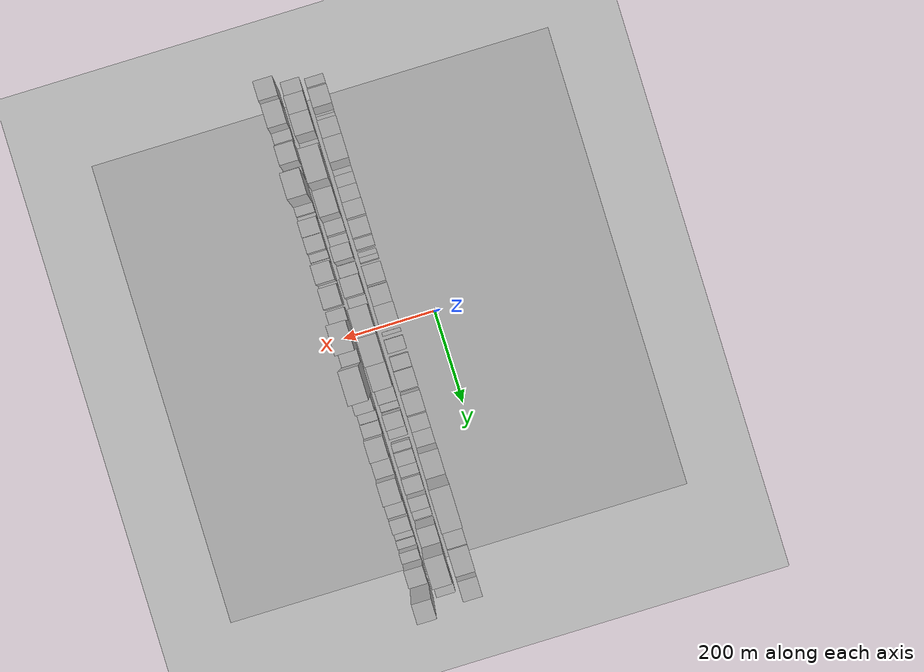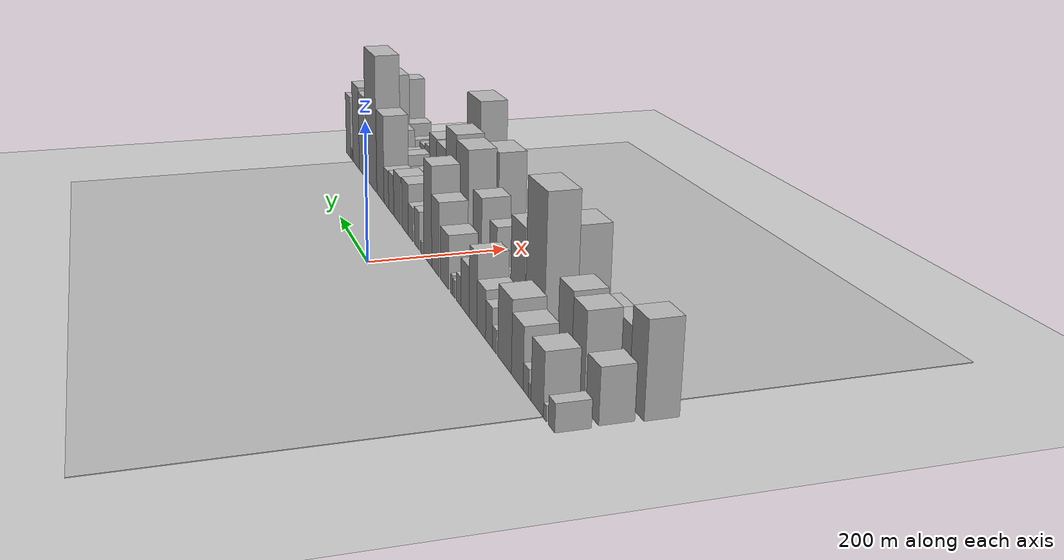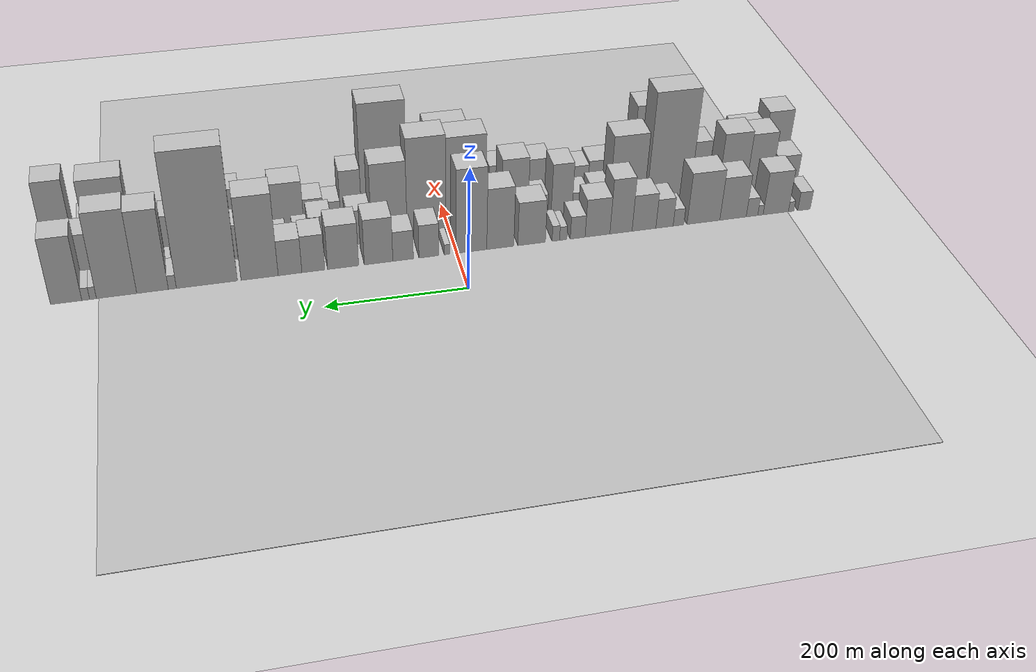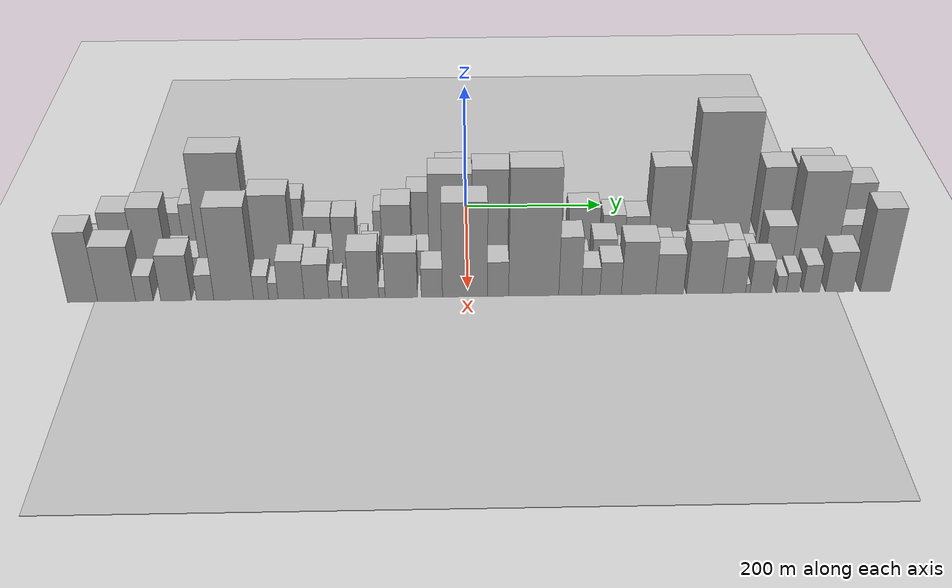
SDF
<?xml version="1.0" encoding="utf-8"?>

<sdf version="1.6">

   <world name="default">

      <gui fullscreen="0">

         <camera name="user_camera">

            <pose>-15 0 4.57585 0 0 0</pose>

            <view_controller>orbit</view_controller>

         </camera>

      </gui>

      <scene>

         <sky>

           <clouds>

             <speed>12</speed>

           </clouds>

         </sky>

         <ambient>0.4 0.4 0.4 1</ambient>

         <background>0.7 0.7 0.7 1</background>

         <shadows>1</shadows>

      </scene>

      <gravity>0 0 -9.8066</gravity>

      <magnetic_field>6e-06 2.3e-05 -4.2e-05</magnetic_field>

      <physics default="0" name="default_physics" type="ode">

         <ode>

            <solver>

               <type>quick</type>

               <iters>10</iters>

               <sor>1.0</sor>

               <use_dynamic_moi_rescaling>0</use_dynamic_moi_rescaling>

            </solver>

            <constraints>

               <cfm>0</cfm>

               <erp>0.2</erp>

               <contact_max_correcting_vel>100</contact_max_correcting_vel>

               <contact_surface_layer>0.001</contact_surface_layer>

            </constraints>

         </ode>

         <max_step_size>0.004</max_step_size>

         <real_time_factor>1</real_time_factor>

         <real_time_update_rate>250</real_time_update_rate>

      </physics>

      <light name="sun" type="directional">

         <cast_shadows>1</cast_shadows>

         <pose>0 0 10 0 0 0</pose>

         <diffuse>0.8 0.8 0.8 1</diffuse>

         <specular>0.2 0.2 0.2 1</specular>

         <attenuation>

            <range>1000</range>

            <constant>0.9</constant>

            <linear>0.01</linear>

            <quadratic>0.001</quadratic>

         </attenuation>

         <direction>-0.5 0.1 -0.9</direction>

      </light>

      <include>

         <name>ground_plane_1</name>

         <uri>model://HANNAS_ground_plane</uri>

         <pose>0 0 0  0 0 0</pose>

      </include>

      <include>

         <name>ground_plane_2</name>

         <uri>model://HANNAS_ground_plane</uri>

         <pose>100 0 0  0 0 0</pose>

      </include>

      <model name="building_1">

         <static>1</static>

         <pose frame="">100.0000 -526.1219 0 0.000000 0.000000 0.000000</pose>

         <link name="link">

            <pose frame="">0 0 16.50 0 0 0</pose>

            <collision name="collision">

               <geometry>

                  <box>

                     <size>40.0000 19.7561 33.0000</size>

                  </box>

               </geometry>

               <max_contacts>10</max_contacts>

               <surface>

                  <contact>

                     <ode/>

                  </contact>

                  <bounce/>

                  <friction>

                     <torsional>

                        <ode/>

                     </torsional>

                     <ode/>

                  </friction>

               </surface>

            </collision>

            <visual name="visual">

               <cast_shadows>0</cast_shadows>

               <geometry>

                  <box>

                     <size>40.0000 19.7561 33.0000</size>

                  </box>

               </geometry>

               <material>

                  <script>

                     <uri>model://HANNAS_wall/materials/scripts</uri>

                     <uri>model://HANNAS_wall/materials/textures</uri>

                     <name>vrc/HANNAS_wall</name>

                  </script>

               </material>

            </visual>

            <self_collide>0</self_collide>

            <enable_wind>0</enable_wind>

            <kinematic>0</kinematic>

         </link>

      </model>

      <model name="building_2">

         <static>1</static>

         <pose frame="">100.0000 -505.8128 0 0.000000 0.000000 0.000000</pose>

         <link name="link">

            <pose frame="">0 0 9.00 0 0 0</pose>

            <collision name="collision">

               <geometry>

                  <box>

                     <size>40.0000 8.8621 18.0000</size>

                  </box>

               </geometry>

               <max_contacts>10</max_contacts>

               <surface>

                  <contact>

                     <ode/>

                  </contact>

                  <bounce/>

                  <friction>

                     <torsional>

                        <ode/>

                     </torsional>

                     <ode/>

                  </friction>

               </surface>

            </collision>

            <visual name="visual">

               <cast_shadows>0</cast_shadows>

               <geometry>

                  <box>

                     <size>40.0000 8.8621 18.0000</size>

                  </box>

               </geometry>

               <material>

                  <script>

                     <uri>model://HANNAS_wall/materials/scripts</uri>

                     <uri>model://HANNAS_wall/materials/textures</uri>

                     <name>vrc/HANNAS_wall</name>

                  </script>

               </material>

            </visual>

            <self_collide>0</self_collide>

            <enable_wind>0</enable_wind>

            <kinematic>0</kinematic>

         </link>

      </model>

      <model name="building_3">

         <static>1</static>

         <pose frame="">100.0000 -481.4801 0 0.000000 0.000000 0.000000</pose>

         <link name="link">

            <pose frame="">0 0 37.50 0 0 0</pose>

            <collision name="collision">

               <geometry>

                  <box>

                     <size>40.0000 39.8033 75.0000</size>

                  </box>

               </geometry>

               <max_contacts>10</max_contacts>

               <surface>

                  <contact>

                     <ode/>

                  </contact>

                  <bounce/>

                  <friction>

                     <torsional>

                        <ode/>

                     </torsional>

                     <ode/>

                  </friction>

               </surface>

            </collision>

            <visual name="visual">

               <cast_shadows>0</cast_shadows>

               <geometry>

                  <box>

                     <size>40.0000 39.8033 75.0000</size>

                  </box>

               </geometry>

               <material>

                  <script>

                     <uri>model://HANNAS_wall/materials/scripts</uri>

                     <uri>model://HANNAS_wall/materials/textures</uri>

                     <name>vrc/HANNAS_wall</name>

                  </script>

               </material>

            </visual>

            <self_collide>0</self_collide>

            <enable_wind>0</enable_wind>

            <kinematic>0</kinematic>

         </link>

      </model>

      <model name="building_4">

         <static>1</static>

         <pose frame="">100.0000 -457.4161 0 0.000000 0.000000 0.000000</pose>

         <link name="link">

            <pose frame="">0 0 9.00 0 0 0</pose>

            <collision name="collision">

               <geometry>

                  <box>

                     <size>40.0000 8.3246 18.0000</size>

                  </box>

               </geometry>

               <max_contacts>10</max_contacts>

               <surface>

                  <contact>

                     <ode/>

                  </contact>

                  <bounce/>

                  <friction>

                     <torsional>

                        <ode/>

                     </torsional>

                     <ode/>

                  </friction>

               </surface>

            </collision>

            <visual name="visual">

               <cast_shadows>0</cast_shadows>

               <geometry>

                  <box>

                     <size>40.0000 8.3246 18.0000</size>

                  </box>

               </geometry>

               <material>

                  <script>

                     <uri>model://HANNAS_wall/materials/scripts</uri>

                     <uri>model://HANNAS_wall/materials/textures</uri>

                     <name>vrc/HANNAS_wall</name>

                  </script>

               </material>

            </visual>

            <self_collide>0</self_collide>

            <enable_wind>0</enable_wind>

            <kinematic>0</kinematic>

         </link>

      </model>

      <model name="building_5">

         <static>1</static>

         <pose frame="">100.0000 -444.1936 0 0.000000 0.000000 0.000000</pose>

         <link name="link">

            <pose frame="">0 0 16.50 0 0 0</pose>

            <collision name="collision">

               <geometry>

                  <box>

                     <size>40.0000 18.1203 33.0000</size>

                  </box>

               </geometry>

               <max_contacts>10</max_contacts>

               <surface>

                  <contact>

                     <ode/>

                  </contact>

                  <bounce/>

                  <friction>

                     <torsional>

                        <ode/>

                     </torsional>

                     <ode/>

                  </friction>

               </surface>

            </collision>

            <visual name="visual">

               <cast_shadows>0</cast_shadows>

               <geometry>

                  <box>

                     <size>40.0000 18.1203 33.0000</size>

                  </box>

               </geometry>

               <material>

                  <script>

                     <uri>model://HANNAS_wall/materials/scripts</uri>

                     <uri>model://HANNAS_wall/materials/textures</uri>

                     <name>vrc/HANNAS_wall</name>

                  </script>

               </material>

            </visual>

            <self_collide>0</self_collide>

            <enable_wind>0</enable_wind>

            <kinematic>0</kinematic>

         </link>

      </model>

      <model name="building_6">

         <static>1</static>

         <pose frame="">100.0000 -414.6209 0 0.000000 0.000000 0.000000</pose>

         <link name="link">

            <pose frame="">0 0 37.50 0 0 0</pose>

            <collision name="collision">

               <geometry>

                  <box>

                     <size>40.0000 41.0252 75.0000</size>

                  </box>

               </geometry>

               <max_contacts>10</max_contacts>

               <surface>

                  <contact>

                     <ode/>

                  </contact>

                  <bounce/>

                  <friction>

                     <torsional>

                        <ode/>

                     </torsional>

                     <ode/>

                  </friction>

               </surface>

            </collision>

            <visual name="visual">

               <cast_shadows>0</cast_shadows>

               <geometry>

                  <box>

                     <size>40.0000 41.0252 75.0000</size>

                  </box>

               </geometry>

               <material>

                  <script>

                     <uri>model://HANNAS_wall/materials/scripts</uri>

                     <uri>model://HANNAS_wall/materials/textures</uri>

                     <name>vrc/HANNAS_wall</name>

                  </script>

               </material>

            </visual>

            <self_collide>0</self_collide>

            <enable_wind>0</enable_wind>

            <kinematic>0</kinematic>

         </link>

      </model>

      <model name="building_7">

         <static>1</static>

         <pose frame="">100.0000 -368.7851 0 0.000000 0.000000 0.000000</pose>

         <link name="link">

            <pose frame="">0 0 45.00 0 0 0</pose>

            <collision name="collision">

               <geometry>

                  <box>

                     <size>40.0000 50.6465 90.0000</size>

                  </box>

               </geometry>

               <max_contacts>10</max_contacts>

               <surface>

                  <contact>

                     <ode/>

                  </contact>

                  <bounce/>

                  <friction>

                     <torsional>

                        <ode/>

                     </torsional>

                     <ode/>

                  </friction>

               </surface>

            </collision>

            <visual name="visual">

               <cast_shadows>0</cast_shadows>

               <geometry>

                  <box>

                     <size>40.0000 50.6465 90.0000</size>

                  </box>

               </geometry>

               <material>

                  <script>

                     <uri>model://HANNAS_wall/materials/scripts</uri>

                     <uri>model://HANNAS_wall/materials/textures</uri>

                     <name>vrc/HANNAS_wall</name>

                  </script>

               </material>

            </visual>

            <self_collide>0</self_collide>

            <enable_wind>0</enable_wind>

            <kinematic>0</kinematic>

         </link>

      </model>

      <model name="building_8">

         <static>1</static>

         <pose frame="">100.0000 -330.3271 0 0.000000 0.000000 0.000000</pose>

         <link name="link">

            <pose frame="">0 0 15.00 0 0 0</pose>

            <collision name="collision">

               <geometry>

                  <box>

                     <size>40.0000 16.2695 30.0000</size>

                  </box>

               </geometry>

               <max_contacts>10</max_contacts>

               <surface>

                  <contact>

                     <ode/>

                  </contact>

                  <bounce/>

                  <friction>

                     <torsional>

                        <ode/>

                     </torsional>

                     <ode/>

                  </friction>

               </surface>

            </collision>

            <visual name="visual">

               <cast_shadows>0</cast_shadows>

               <geometry>

                  <box>

                     <size>40.0000 16.2695 30.0000</size>

                  </box>

               </geometry>

               <material>

                  <script>

                     <uri>model://HANNAS_wall/materials/scripts</uri>

                     <uri>model://HANNAS_wall/materials/textures</uri>

                     <name>vrc/HANNAS_wall</name>

                  </script>

               </material>

            </visual>

            <self_collide>0</self_collide>

            <enable_wind>0</enable_wind>

            <kinematic>0</kinematic>

         </link>

      </model>

      <model name="building_9">

         <static>1</static>

         <pose frame="">100.0000 -308.9415 0 0.000000 0.000000 0.000000</pose>

         <link name="link">

            <pose frame="">0 0 25.50 0 0 0</pose>

            <collision name="collision">

               <geometry>

                  <box>

                     <size>40.0000 26.5016 51.0000</size>

                  </box>

               </geometry>

               <max_contacts>10</max_contacts>

               <surface>

                  <contact>

                     <ode/>

                  </contact>

                  <bounce/>

                  <friction>

                     <torsional>

                        <ode/>

                     </torsional>

                     <ode/>

                  </friction>

               </surface>

            </collision>

            <visual name="visual">

               <cast_shadows>0</cast_shadows>

               <geometry>

                  <box>

                     <size>40.0000 26.5016 51.0000</size>

                  </box>

               </geometry>

               <material>

                  <script>

                     <uri>model://HANNAS_wall/materials/scripts</uri>

                     <uri>model://HANNAS_wall/materials/textures</uri>

                     <name>vrc/HANNAS_wall</name>

                  </script>

               </material>

            </visual>

            <self_collide>0</self_collide>

            <enable_wind>0</enable_wind>

            <kinematic>0</kinematic>

         </link>

      </model>

      <model name="building_10">

         <static>1</static>

         <pose frame="">100.0000 -277.5802 0 0.000000 0.000000 0.000000</pose>

         <link name="link">

            <pose frame="">0 0 31.50 0 0 0</pose>

            <collision name="collision">

               <geometry>

                  <box>

                     <size>40.0000 36.2212 63.0000</size>

                  </box>

               </geometry>

               <max_contacts>10</max_contacts>

               <surface>

                  <contact>

                     <ode/>

                  </contact>

                  <bounce/>

                  <friction>

                     <torsional>

                        <ode/>

                     </torsional>

                     <ode/>

                  </friction>

               </surface>

            </collision>

            <visual name="visual">

               <cast_shadows>0</cast_shadows>

               <geometry>

                  <box>

                     <size>40.0000 36.2212 63.0000</size>

                  </box>

               </geometry>

               <material>

                  <script>

                     <uri>model://HANNAS_wall/materials/scripts</uri>

                     <uri>model://HANNAS_wall/materials/textures</uri>

                     <name>vrc/HANNAS_wall</name>

                  </script>

               </material>

            </visual>

            <self_collide>0</self_collide>

            <enable_wind>0</enable_wind>

            <kinematic>0</kinematic>

         </link>

      </model>

      <model name="building_11">

         <static>1</static>

         <pose frame="">100.0000 -242.7099 0 0.000000 0.000000 0.000000</pose>

         <link name="link">

            <pose frame="">0 0 48.00 0 0 0</pose>

            <collision name="collision">

               <geometry>

                  <box>

                     <size>40.0000 33.5194 96.0000</size>

                  </box>

               </geometry>

               <max_contacts>10</max_contacts>

               <surface>

                  <contact>

                     <ode/>

                  </contact>

                  <bounce/>

                  <friction>

                     <torsional>

                        <ode/>

                     </torsional>

                     <ode/>

                  </friction>

               </surface>

            </collision>

            <visual name="visual">

               <cast_shadows>0</cast_shadows>

               <geometry>

                  <box>

                     <size>40.0000 33.5194 96.0000</size>

                  </box>

               </geometry>

               <material>

                  <script>

                     <uri>model://HANNAS_wall/materials/scripts</uri>

                     <uri>model://HANNAS_wall/materials/textures</uri>

                     <name>vrc/HANNAS_wall</name>

                  </script>

               </material>

            </visual>

            <self_collide>0</self_collide>

            <enable_wind>0</enable_wind>

            <kinematic>0</kinematic>

         </link>

      </model>

      <model name="building_12">

         <static>1</static>

         <pose frame="">100.0000 -207.3057 0 0.000000 0.000000 0.000000</pose>

         <link name="link">

            <pose frame="">0 0 33.00 0 0 0</pose>

            <collision name="collision">

               <geometry>

                  <box>

                     <size>40.0000 37.2890 66.0000</size>

                  </box>

               </geometry>

               <max_contacts>10</max_contacts>

               <surface>

                  <contact>

                     <ode/>

                  </contact>

                  <bounce/>

                  <friction>

                     <torsional>

                        <ode/>

                     </torsional>

                     <ode/>

                  </friction>

               </surface>

            </collision>

            <visual name="visual">

               <cast_shadows>0</cast_shadows>

               <geometry>

                  <box>

                     <size>40.0000 37.2890 66.0000</size>

                  </box>

               </geometry>

               <material>

                  <script>

                     <uri>model://HANNAS_wall/materials/scripts</uri>

                     <uri>model://HANNAS_wall/materials/textures</uri>

                     <name>vrc/HANNAS_wall</name>

                  </script>

               </material>

            </visual>

            <self_collide>0</self_collide>

            <enable_wind>0</enable_wind>

            <kinematic>0</kinematic>

         </link>

      </model>

      <model name="building_13">

         <static>1</static>

         <pose frame="">100.0000 -177.5530 0 0.000000 0.000000 0.000000</pose>

         <link name="link">

            <pose frame="">0 0 19.50 0 0 0</pose>

            <collision name="collision">

               <geometry>

                  <box>

                     <size>40.0000 22.2164 39.0000</size>

                  </box>

               </geometry>

               <max_contacts>10</max_contacts>

               <surface>

                  <contact>

                     <ode/>

                  </contact>

                  <bounce/>

                  <friction>

                     <torsional>

                        <ode/>

                     </torsional>

                     <ode/>

                  </friction>

               </surface>

            </collision>

            <visual name="visual">

               <cast_shadows>0</cast_shadows>

               <geometry>

                  <box>

                     <size>40.0000 22.2164 39.0000</size>

                  </box>

               </geometry>

               <material>

                  <script>

                     <uri>model://HANNAS_wall/materials/scripts</uri>

                     <uri>model://HANNAS_wall/materials/textures</uri>

                     <name>vrc/HANNAS_wall</name>

                  </script>

               </material>

            </visual>

            <self_collide>0</self_collide>

            <enable_wind>0</enable_wind>

            <kinematic>0</kinematic>

         </link>

      </model>

      <model name="building_14">

         <static>1</static>

         <pose frame="">100.0000 -155.9474 0 0.000000 0.000000 0.000000</pose>

         <link name="link">

            <pose frame="">0 0 12.00 0 0 0</pose>

            <collision name="collision">

               <geometry>

                  <box>

                     <size>40.0000 10.9948 24.0000</size>

                  </box>

               </geometry>

               <max_contacts>10</max_contacts>

               <surface>

                  <contact>

                     <ode/>

                  </contact>

                  <bounce/>

                  <friction>

                     <torsional>

                        <ode/>

                     </torsional>

                     <ode/>

                  </friction>

               </surface>

            </collision>

            <visual name="visual">

               <cast_shadows>0</cast_shadows>

               <geometry>

                  <box>

                     <size>40.0000 10.9948 24.0000</size>

                  </box>

               </geometry>

               <material>

                  <script>

                     <uri>model://HANNAS_wall/materials/scripts</uri>

                     <uri>model://HANNAS_wall/materials/textures</uri>

                     <name>vrc/HANNAS_wall</name>

                  </script>

               </material>

            </visual>

            <self_collide>0</self_collide>

            <enable_wind>0</enable_wind>

            <kinematic>0</kinematic>

         </link>

      </model>

      <model name="building_15">

         <static>1</static>

         <pose frame="">100.0000 -144.8845 0 0.000000 0.000000 0.000000</pose>

         <link name="link">

            <pose frame="">0 0 13.50 0 0 0</pose>

            <collision name="collision">

               <geometry>

                  <box>

                     <size>40.0000 11.1311 27.0000</size>

                  </box>

               </geometry>

               <max_contacts>10</max_contacts>

               <surface>

                  <contact>

                     <ode/>

                  </contact>

                  <bounce/>

                  <friction>

                     <torsional>

                        <ode/>

                     </torsional>

                     <ode/>

                  </friction>

               </surface>

            </collision>

            <visual name="visual">

               <cast_shadows>0</cast_shadows>

               <geometry>

                  <box>

                     <size>40.0000 11.1311 27.0000</size>

                  </box>

               </geometry>

               <material>

                  <script>

                     <uri>model://HANNAS_wall/materials/scripts</uri>

                     <uri>model://HANNAS_wall/materials/textures</uri>

                     <name>vrc/HANNAS_wall</name>

                  </script>

               </material>

            </visual>

            <self_collide>0</self_collide>

            <enable_wind>0</enable_wind>

            <kinematic>0</kinematic>

         </link>

      </model>

      <model name="building_16">

         <static>1</static>

         <pose frame="">100.0000 -108.9709 0 0.000000 0.000000 0.000000</pose>

         <link name="link">

            <pose frame="">0 0 37.50 0 0 0</pose>

            <collision name="collision">

               <geometry>

                  <box>

                     <size>40.0000 40.6960 75.0000</size>

                  </box>

               </geometry>

               <max_contacts>10</max_contacts>

               <surface>

                  <contact>

                     <ode/>

                  </contact>

                  <bounce/>

                  <friction>

                     <torsional>

                        <ode/>

                     </torsional>

                     <ode/>

                  </friction>

               </surface>

            </collision>

            <visual name="visual">

               <cast_shadows>0</cast_shadows>

               <geometry>

                  <box>

                     <size>40.0000 40.6960 75.0000</size>

                  </box>

               </geometry>

               <material>

                  <script>

                     <uri>model://HANNAS_wall/materials/scripts</uri>

                     <uri>model://HANNAS_wall/materials/textures</uri>

                     <name>vrc/HANNAS_wall</name>

                  </script>

               </material>

            </visual>

            <self_collide>0</self_collide>

            <enable_wind>0</enable_wind>

            <kinematic>0</kinematic>

         </link>

      </model>

      <model name="building_17">

         <static>1</static>

         <pose frame="">100.0000 -62.7617 0 0.000000 0.000000 0.000000</pose>

         <link name="link">

            <pose frame="">0 0 52.50 0 0 0</pose>

            <collision name="collision">

               <geometry>

                  <box>

                     <size>40.0000 39.7224 105.0000</size>

                  </box>

               </geometry>

               <max_contacts>10</max_contacts>

               <surface>

                  <contact>

                     <ode/>

                  </contact>

                  <bounce/>

                  <friction>

                     <torsional>

                        <ode/>

                     </torsional>

                     <ode/>

                  </friction>

               </surface>

            </collision>

            <visual name="visual">

               <cast_shadows>0</cast_shadows>

               <geometry>

                  <box>

                     <size>40.0000 39.7224 105.0000</size>

                  </box>

               </geometry>

               <material>

                  <script>

                     <uri>model://HANNAS_wall/materials/scripts</uri>

                     <uri>model://HANNAS_wall/materials/textures</uri>

                     <name>vrc/HANNAS_wall</name>

                  </script>

               </material>

            </visual>

            <self_collide>0</self_collide>

            <enable_wind>0</enable_wind>

            <kinematic>0</kinematic>

         </link>

      </model>

      <model name="building_18">

         <static>1</static>

         <pose frame="">100.0000 -20.6462 0 0.000000 0.000000 0.000000</pose>

         <link name="link">

            <pose frame="">0 0 72.00 0 0 0</pose>

            <collision name="collision">

               <geometry>

                  <box>

                     <size>40.0000 44.5086 144.0000</size>

                  </box>

               </geometry>

               <max_contacts>10</max_contacts>

               <surface>

                  <contact>

                     <ode/>

                  </contact>

                  <bounce/>

                  <friction>

                     <torsional>

                        <ode/>

                     </torsional>

                     <ode/>

                  </friction>

               </surface>

            </collision>

            <visual name="visual">

               <cast_shadows>0</cast_shadows>

               <geometry>

                  <box>

                     <size>40.0000 44.5086 144.0000</size>

                  </box>

               </geometry>

               <material>

                  <script>

                     <uri>model://HANNAS_wall/materials/scripts</uri>

                     <uri>model://HANNAS_wall/materials/textures</uri>

                     <name>vrc/HANNAS_wall</name>

                  </script>

               </material>

            </visual>

            <self_collide>0</self_collide>

            <enable_wind>0</enable_wind>

            <kinematic>0</kinematic>

         </link>

      </model>

      <model name="building_19">

         <static>1</static>

         <pose frame="">100.0000 14.7461 0 0.000000 0.000000 0.000000</pose>

         <link name="link">

            <pose frame="">0 0 9.00 0 0 0</pose>

            <collision name="collision">

               <geometry>

                  <box>

                     <size>40.0000 8.2760 18.0000</size>

                  </box>

               </geometry>

               <max_contacts>10</max_contacts>

               <surface>

                  <contact>

                     <ode/>

                  </contact>

                  <bounce/>

                  <friction>

                     <torsional>

                        <ode/>

                     </torsional>

                     <ode/>

                  </friction>

               </surface>

            </collision>

            <visual name="visual">

               <cast_shadows>0</cast_shadows>

               <geometry>

                  <box>

                     <size>40.0000 8.2760 18.0000</size>

                  </box>

               </geometry>

               <material>

                  <script>

                     <uri>model://HANNAS_wall/materials/scripts</uri>

                     <uri>model://HANNAS_wall/materials/textures</uri>

                     <name>vrc/HANNAS_wall</name>

                  </script>

               </material>

            </visual>

            <self_collide>0</self_collide>

            <enable_wind>0</enable_wind>

            <kinematic>0</kinematic>

         </link>

      </model>

      <model name="building_20">

         <static>1</static>

         <pose frame="">100.0000 41.2204 0 0.000000 0.000000 0.000000</pose>

         <link name="link">

            <pose frame="">0 0 28.50 0 0 0</pose>

            <collision name="collision">

               <geometry>

                  <box>

                     <size>40.0000 28.6727 57.0000</size>

                  </box>

               </geometry>

               <max_contacts>10</max_contacts>

               <surface>

                  <contact>

                     <ode/>

                  </contact>

                  <bounce/>

                  <friction>

                     <torsional>

                        <ode/>

                     </torsional>

                     <ode/>

                  </friction>

               </surface>

            </collision>

            <visual name="visual">

               <cast_shadows>0</cast_shadows>

               <geometry>

                  <box>

                     <size>40.0000 28.6727 57.0000</size>

                  </box>

               </geometry>

               <material>

                  <script>

                     <uri>model://HANNAS_wall/materials/scripts</uri>

                     <uri>model://HANNAS_wall/materials/textures</uri>

                     <name>vrc/HANNAS_wall</name>

                  </script>

               </material>

            </visual>

            <self_collide>0</self_collide>

            <enable_wind>0</enable_wind>

            <kinematic>0</kinematic>

         </link>

      </model>

      <model name="building_21">

         <static>1</static>

         <pose frame="">100.0000 78.3445 0 0.000000 0.000000 0.000000</pose>

         <link name="link">

            <pose frame="">0 0 25.50 0 0 0</pose>

            <collision name="collision">

               <geometry>

                  <box>

                     <size>40.0000 29.5755 51.0000</size>

                  </box>

               </geometry>

               <max_contacts>10</max_contacts>

               <surface>

                  <contact>

                     <ode/>

                  </contact>

                  <bounce/>

                  <friction>

                     <torsional>

                        <ode/>

                     </torsional>

                     <ode/>

                  </friction>

               </surface>

            </collision>

            <visual name="visual">

               <cast_shadows>0</cast_shadows>

               <geometry>

                  <box>

                     <size>40.0000 29.5755 51.0000</size>

                  </box>

               </geometry>

               <material>

                  <script>

                     <uri>model://HANNAS_wall/materials/scripts</uri>

                     <uri>model://HANNAS_wall/materials/textures</uri>

                     <name>vrc/HANNAS_wall</name>

                  </script>

               </material>

            </visual>

            <self_collide>0</self_collide>

            <enable_wind>0</enable_wind>

            <kinematic>0</kinematic>

         </link>

      </model>

      <model name="building_22">

         <static>1</static>

         <pose frame="">100.0000 113.4682 0 0.000000 0.000000 0.000000</pose>

         <link name="link">

            <pose frame="">0 0 39.00 0 0 0</pose>

            <collision name="collision">

               <geometry>

                  <box>

                     <size>40.0000 40.6719 78.0000</size>

                  </box>

               </geometry>

               <max_contacts>10</max_contacts>

               <surface>

                  <contact>

                     <ode/>

                  </contact>

                  <bounce/>

                  <friction>

                     <torsional>

                        <ode/>

                     </torsional>

                     <ode/>

                  </friction>

               </surface>

            </collision>

            <visual name="visual">

               <cast_shadows>0</cast_shadows>

               <geometry>

                  <box>

                     <size>40.0000 40.6719 78.0000</size>

                  </box>

               </geometry>

               <material>

                  <script>

                     <uri>model://HANNAS_wall/materials/scripts</uri>

                     <uri>model://HANNAS_wall/materials/textures</uri>

                     <name>vrc/HANNAS_wall</name>

                  </script>

               </material>

            </visual>

            <self_collide>0</self_collide>

            <enable_wind>0</enable_wind>

            <kinematic>0</kinematic>

         </link>

      </model>

      <model name="building_23">

         <static>1</static>

         <pose frame="">100.0000 163.7614 0 0.000000 0.000000 0.000000</pose>

         <link name="link">

            <pose frame="">0 0 37.50 0 0 0</pose>

            <collision name="collision">

               <geometry>

                  <box>

                     <size>40.0000 43.9146 75.0000</size>

                  </box>

               </geometry>

               <max_contacts>10</max_contacts>

               <surface>

                  <contact>

                     <ode/>

                  </contact>

                  <bounce/>

                  <friction>

                     <torsional>

                        <ode/>

                     </torsional>

                     <ode/>

                  </friction>

               </surface>

            </collision>

            <visual name="visual">

               <cast_shadows>0</cast_shadows>

               <geometry>

                  <box>

                     <size>40.0000 43.9146 75.0000</size>

                  </box>

               </geometry>

               <material>

                  <script>

                     <uri>model://HANNAS_wall/materials/scripts</uri>

                     <uri>model://HANNAS_wall/materials/textures</uri>

                     <name>vrc/HANNAS_wall</name>

                  </script>

               </material>

            </visual>

            <self_collide>0</self_collide>

            <enable_wind>0</enable_wind>

            <kinematic>0</kinematic>

         </link>

      </model>

      <model name="building_24">

         <static>1</static>

         <pose frame="">100.0000 205.7868 0 0.000000 0.000000 0.000000</pose>

         <link name="link">

            <pose frame="">0 0 31.50 0 0 0</pose>

            <collision name="collision">

               <geometry>

                  <box>

                     <size>40.0000 32.1361 63.0000</size>

                  </box>

               </geometry>

               <max_contacts>10</max_contacts>

               <surface>

                  <contact>

                     <ode/>

                  </contact>

                  <bounce/>

                  <friction>

                     <torsional>

                        <ode/>

                     </torsional>

                     <ode/>

                  </friction>

               </surface>

            </collision>

            <visual name="visual">

               <cast_shadows>0</cast_shadows>

               <geometry>

                  <box>

                     <size>40.0000 32.1361 63.0000</size>

                  </box>

               </geometry>

               <material>

                  <script>

                     <uri>model://HANNAS_wall/materials/scripts</uri>

                     <uri>model://HANNAS_wall/materials/textures</uri>

                     <name>vrc/HANNAS_wall</name>

                  </script>

               </material>

            </visual>

            <self_collide>0</self_collide>

            <enable_wind>0</enable_wind>

            <kinematic>0</kinematic>

         </link>

      </model>

      <model name="building_25">

         <static>1</static>

         <pose frame="">100.0000 238.4247 0 0.000000 0.000000 0.000000</pose>

         <link name="link">

            <pose frame="">0 0 30.00 0 0 0</pose>

            <collision name="collision">

               <geometry>

                  <box>

                     <size>40.0000 33.1398 60.0000</size>

                  </box>

               </geometry>

               <max_contacts>10</max_contacts>

               <surface>

                  <contact>

                     <ode/>

                  </contact>

                  <bounce/>

                  <friction>

                     <torsional>

                        <ode/>

                     </torsional>

                     <ode/>

                  </friction>

               </surface>

            </collision>

            <visual name="visual">

               <cast_shadows>0</cast_shadows>

               <geometry>

                  <box>

                     <size>40.0000 33.1398 60.0000</size>

                  </box>

               </geometry>

               <material>

                  <script>

                     <uri>model://HANNAS_wall/materials/scripts</uri>

                     <uri>model://HANNAS_wall/materials/textures</uri>

                     <name>vrc/HANNAS_wall</name>

                  </script>

               </material>

            </visual>

            <self_collide>0</self_collide>

            <enable_wind>0</enable_wind>

            <kinematic>0</kinematic>

         </link>

      </model>

      <model name="building_26">

         <static>1</static>

         <pose frame="">100.0000 280.7646 0 0.000000 0.000000 0.000000</pose>

         <link name="link">

            <pose frame="">0 0 70.50 0 0 0</pose>

            <collision name="collision">

               <geometry>

                  <box>

                     <size>40.0000 51.5401 141.0000</size>

                  </box>

               </geometry>

               <max_contacts>10</max_contacts>

               <surface>

                  <contact>

                     <ode/>

                  </contact>

                  <bounce/>

                  <friction>

                     <torsional>

                        <ode/>

                     </torsional>

                     <ode/>

                  </friction>

               </surface>

            </collision>

            <visual name="visual">

               <cast_shadows>0</cast_shadows>

               <geometry>

                  <box>

                     <size>40.0000 51.5401 141.0000</size>

                  </box>

               </geometry>

               <material>

                  <script>

                     <uri>model://HANNAS_wall/materials/scripts</uri>

                     <uri>model://HANNAS_wall/materials/textures</uri>

                     <name>vrc/HANNAS_wall</name>

                  </script>

               </material>

            </visual>

            <self_collide>0</self_collide>

            <enable_wind>0</enable_wind>

            <kinematic>0</kinematic>

         </link>

      </model>

      <model name="building_27">

         <static>1</static>

         <pose frame="">100.0000 353.3509 0 0.000000 0.000000 0.000000</pose>

         <link name="link">

            <pose frame="">0 0 112.50 0 0 0</pose>

            <collision name="collision">

               <geometry>

                  <box>

                     <size>40.0000 83.6324 225.0000</size>

                  </box>

               </geometry>

               <max_contacts>10</max_contacts>

               <surface>

                  <contact>

                     <ode/>

                  </contact>

                  <bounce/>

                  <friction>

                     <torsional>

                        <ode/>

                     </torsional>

                     <ode/>

                  </friction>

               </surface>

            </collision>

            <visual name="visual">

               <cast_shadows>0</cast_shadows>

               <geometry>

                  <box>

                     <size>40.0000 83.6324 225.0000</size>

                  </box>

               </geometry>

               <material>

                  <script>

                     <uri>model://HANNAS_wall/materials/scripts</uri>

                     <uri>model://HANNAS_wall/materials/textures</uri>

                     <name>vrc/HANNAS_wall</name>

                  </script>

               </material>

            </visual>

            <self_collide>0</self_collide>

            <enable_wind>0</enable_wind>

            <kinematic>0</kinematic>

         </link>

      </model>

      <model name="building_28">

         <static>1</static>

         <pose frame="">100.0000 400.6834 0 0.000000 0.000000 0.000000</pose>

         <link name="link">

            <pose frame="">0 0 12.00 0 0 0</pose>

            <collision name="collision">

               <geometry>

                  <box>

                     <size>40.0000 11.0327 24.0000</size>

                  </box>

               </geometry>

               <max_contacts>10</max_contacts>

               <surface>

                  <contact>

                     <ode/>

                  </contact>

                  <bounce/>

                  <friction>

                     <torsional>

                        <ode/>

                     </torsional>

                     <ode/>

                  </friction>

               </surface>

            </collision>

            <visual name="visual">

               <cast_shadows>0</cast_shadows>

               <geometry>

                  <box>

                     <size>40.0000 11.0327 24.0000</size>

                  </box>

               </geometry>

               <material>

                  <script>

                     <uri>model://HANNAS_wall/materials/scripts</uri>

                     <uri>model://HANNAS_wall/materials/textures</uri>

                     <name>vrc/HANNAS_wall</name>

                  </script>

               </material>

            </visual>

            <self_collide>0</self_collide>

            <enable_wind>0</enable_wind>

            <kinematic>0</kinematic>

         </link>

      </model>

      <model name="building_29">

         <static>1</static>

         <pose frame="">100.0000 427.5657 0 0.000000 0.000000 0.000000</pose>

         <link name="link">

            <pose frame="">0 0 69.00 0 0 0</pose>

            <collision name="collision">

               <geometry>

                  <box>

                     <size>40.0000 42.7318 138.0000</size>

                  </box>

               </geometry>

               <max_contacts>10</max_contacts>

               <surface>

                  <contact>

                     <ode/>

                  </contact>

                  <bounce/>

                  <friction>

                     <torsional>

                        <ode/>

                     </torsional>

                     <ode/>

                  </friction>

               </surface>

            </collision>

            <visual name="visual">

               <cast_shadows>0</cast_shadows>

               <geometry>

                  <box>

                     <size>40.0000 42.7318 138.0000</size>

                  </box>

               </geometry>

               <material>

                  <script>

                     <uri>model://HANNAS_wall/materials/scripts</uri>

                     <uri>model://HANNAS_wall/materials/textures</uri>

                     <name>vrc/HANNAS_wall</name>

                  </script>

               </material>

            </visual>

            <self_collide>0</self_collide>

            <enable_wind>0</enable_wind>

            <kinematic>0</kinematic>

         </link>

      </model>

      <model name="building_30">

         <static>1</static>

         <pose frame="">100.0000 476.0286 0 0.000000 0.000000 0.000000</pose>

         <link name="link">

            <pose frame="">0 0 72.00 0 0 0</pose>

            <collision name="collision">

               <geometry>

                  <box>

                     <size>40.0000 54.1939 144.0000</size>

                  </box>

               </geometry>

               <max_contacts>10</max_contacts>

               <surface>

                  <contact>

                     <ode/>

                  </contact>

                  <bounce/>

                  <friction>

                     <torsional>

                        <ode/>

                     </torsional>

                     <ode/>

                  </friction>

               </surface>

            </collision>

            <visual name="visual">

               <cast_shadows>0</cast_shadows>

               <geometry>

                  <box>

                     <size>40.0000 54.1939 144.0000</size>

                  </box>

               </geometry>

               <material>

                  <script>

                     <uri>model://HANNAS_wall/materials/scripts</uri>

                     <uri>model://HANNAS_wall/materials/textures</uri>

                     <name>vrc/HANNAS_wall</name>

                  </script>

               </material>

            </visual>

            <self_collide>0</self_collide>

            <enable_wind>0</enable_wind>

            <kinematic>0</kinematic>

         </link>

      </model>

      <model name="building_31">

         <static>1</static>

         <pose frame="">100.0000 507.6164 0 0.000000 0.000000 0.000000</pose>

         <link name="link">

            <pose frame="">0 0 10.50 0 0 0</pose>

            <collision name="collision">

               <geometry>

                  <box>

                     <size>40.0000 8.9817 21.0000</size>

                  </box>

               </geometry>

               <max_contacts>10</max_contacts>

               <surface>

                  <contact>

                     <ode/>

                  </contact>

                  <bounce/>

                  <friction>

                     <torsional>

                        <ode/>

                     </torsional>

                     <ode/>

                  </friction>

               </surface>

            </collision>

            <visual name="visual">

               <cast_shadows>0</cast_shadows>

               <geometry>

                  <box>

                     <size>40.0000 8.9817 21.0000</size>

                  </box>

               </geometry>

               <material>

                  <script>

                     <uri>model://HANNAS_wall/materials/scripts</uri>

                     <uri>model://HANNAS_wall/materials/textures</uri>

                     <name>vrc/HANNAS_wall</name>

                  </script>

               </material>

            </visual>

            <self_collide>0</self_collide>

            <enable_wind>0</enable_wind>

            <kinematic>0</kinematic>

         </link>

      </model>

      <model name="building_32">

         <static>1</static>

         <pose frame="">100.0000 517.3540 0 0.000000 0.000000 0.000000</pose>

         <link name="link">

            <pose frame="">0 0 10.50 0 0 0</pose>

            <collision name="collision">

               <geometry>

                  <box>

                     <size>40.0000 10.4935 21.0000</size>

                  </box>

               </geometry>

               <max_contacts>10</max_contacts>

               <surface>

                  <contact>

                     <ode/>

                  </contact>

                  <bounce/>

                  <friction>

                     <torsional>

                        <ode/>

                     </torsional>

                     <ode/>

                  </friction>

               </surface>

            </collision>

            <visual name="visual">

               <cast_shadows>0</cast_shadows>

               <geometry>

                  <box>

                     <size>40.0000 10.4935 21.0000</size>

                  </box>

               </geometry>

               <material>

                  <script>

                     <uri>model://HANNAS_wall/materials/scripts</uri>

                     <uri>model://HANNAS_wall/materials/textures</uri>

                     <name>vrc/HANNAS_wall</name>

                  </script>

               </material>

            </visual>

            <self_collide>0</self_collide>

            <enable_wind>0</enable_wind>

            <kinematic>0</kinematic>

         </link>

      </model>

      <model name="building_33">

         <static>1</static>

         <pose frame="">100.0000 543.4037 0 0.000000 0.000000 0.000000</pose>

         <link name="link">

            <pose frame="">0 0 55.50 0 0 0</pose>

            <collision name="collision">

               <geometry>

                  <box>

                     <size>40.0000 41.6059 111.0000</size>

                  </box>

               </geometry>

               <max_contacts>10</max_contacts>

               <surface>

                  <contact>

                     <ode/>

                  </contact>

                  <bounce/>

                  <friction>

                     <torsional>

                        <ode/>

                     </torsional>

                     <ode/>

                  </friction>

               </surface>

            </collision>

            <visual name="visual">

               <cast_shadows>0</cast_shadows>

               <geometry>

                  <box>

                     <size>40.0000 41.6059 111.0000</size>

                  </box>

               </geometry>

               <material>

                  <script>

                     <uri>model://HANNAS_wall/materials/scripts</uri>

                     <uri>model://HANNAS_wall/materials/textures</uri>

                     <name>vrc/HANNAS_wall</name>

                  </script>

               </material>

            </visual>

            <self_collide>0</self_collide>

            <enable_wind>0</enable_wind>

            <kinematic>0</kinematic>

         </link>

      </model>

      <model name="building_34">

         <static>1</static>

         <pose frame="">149.0000 -514.7943 0 0.000000 0.000000 0.000000</pose>

         <link name="link">

            <pose frame="">0 0 33.00 0 0 0</pose>

            <collision name="collision">

               <geometry>

                  <box>

                     <size>40.0000 36.4115 66.0000</size>

                  </box>

               </geometry>

               <max_contacts>10</max_contacts>

               <surface>

                  <contact>

                     <ode/>

                  </contact>

                  <bounce/>

                  <friction>

                     <torsional>

                        <ode/>

                     </torsional>

                     <ode/>

                  </friction>

               </surface>

            </collision>

            <visual name="visual">

               <cast_shadows>0</cast_shadows>

               <geometry>

                  <box>

                     <size>40.0000 36.4115 66.0000</size>

                  </box>

               </geometry>

               <material>

                  <script>

                     <uri>model://HANNAS_wall/materials/scripts</uri>

                     <uri>model://HANNAS_wall/materials/textures</uri>

                     <name>vrc/HANNAS_wall</name>

                  </script>

               </material>

            </visual>

            <self_collide>0</self_collide>

            <enable_wind>0</enable_wind>

            <kinematic>0</kinematic>

         </link>

      </model>

      <model name="building_35">

         <static>1</static>

         <pose frame="">149.0000 -471.6431 0 0.000000 0.000000 0.000000</pose>

         <link name="link">

            <pose frame="">0 0 55.50 0 0 0</pose>

            <collision name="collision">

               <geometry>

                  <box>

                     <size>40.0000 39.8908 111.0000</size>

                  </box>

               </geometry>

               <max_contacts>10</max_contacts>

               <surface>

                  <contact>

                     <ode/>

                  </contact>

                  <bounce/>

                  <friction>

                     <torsional>

                        <ode/>

                     </torsional>

                     <ode/>

                  </friction>

               </surface>

            </collision>

            <visual name="visual">

               <cast_shadows>0</cast_shadows>

               <geometry>

                  <box>

                     <size>40.0000 39.8908 111.0000</size>

                  </box>

               </geometry>

               <material>

                  <script>

                     <uri>model://HANNAS_wall/materials/scripts</uri>

                     <uri>model://HANNAS_wall/materials/textures</uri>

                     <name>vrc/HANNAS_wall</name>

                  </script>

               </material>

            </visual>

            <self_collide>0</self_collide>

            <enable_wind>0</enable_wind>

            <kinematic>0</kinematic>

         </link>

      </model>

      <model name="building_36">

         <static>1</static>

         <pose frame="">149.0000 -429.7863 0 0.000000 0.000000 0.000000</pose>

         <link name="link">

            <pose frame="">0 0 58.50 0 0 0</pose>

            <collision name="collision">

               <geometry>

                  <box>

                     <size>40.0000 43.8228 117.0000</size>

                  </box>

               </geometry>

               <max_contacts>10</max_contacts>

               <surface>

                  <contact>

                     <ode/>

                  </contact>

                  <bounce/>

                  <friction>

                     <torsional>

                        <ode/>

                     </torsional>

                     <ode/>

                  </friction>

               </surface>

            </collision>

            <visual name="visual">

               <cast_shadows>0</cast_shadows>

               <geometry>

                  <box>

                     <size>40.0000 43.8228 117.0000</size>

                  </box>

               </geometry>

               <material>

                  <script>

                     <uri>model://HANNAS_wall/materials/scripts</uri>

                     <uri>model://HANNAS_wall/materials/textures</uri>

                     <name>vrc/HANNAS_wall</name>

                  </script>

               </material>

            </visual>

            <self_collide>0</self_collide>

            <enable_wind>0</enable_wind>

            <kinematic>0</kinematic>

         </link>

      </model>

      <model name="building_37">

         <static>1</static>

         <pose frame="">149.0000 -395.3865 0 0.000000 0.000000 0.000000</pose>

         <link name="link">

            <pose frame="">0 0 22.50 0 0 0</pose>

            <collision name="collision">

               <geometry>

                  <box>

                     <size>40.0000 24.9768 45.0000</size>

                  </box>

               </geometry>

               <max_contacts>10</max_contacts>

               <surface>

                  <contact>

                     <ode/>

                  </contact>

                  <bounce/>

                  <friction>

                     <torsional>

                        <ode/>

                     </torsional>

                     <ode/>

                  </friction>

               </surface>

            </collision>

            <visual name="visual">

               <cast_shadows>0</cast_shadows>

               <geometry>

                  <box>

                     <size>40.0000 24.9768 45.0000</size>

                  </box>

               </geometry>

               <material>

                  <script>

                     <uri>model://HANNAS_wall/materials/scripts</uri>

                     <uri>model://HANNAS_wall/materials/textures</uri>

                     <name>vrc/HANNAS_wall</name>

                  </script>

               </material>

            </visual>

            <self_collide>0</self_collide>

            <enable_wind>0</enable_wind>

            <kinematic>0</kinematic>

         </link>

      </model>

      <model name="building_38">

         <static>1</static>

         <pose frame="">149.0000 -373.2390 0 0.000000 0.000000 0.000000</pose>

         <link name="link">

            <pose frame="">0 0 18.00 0 0 0</pose>

            <collision name="collision">

               <geometry>

                  <box>

                     <size>40.0000 19.3182 36.0000</size>

                  </box>

               </geometry>

               <max_contacts>10</max_contacts>

               <surface>

                  <contact>

                     <ode/>

                  </contact>

                  <bounce/>

                  <friction>

                     <torsional>

                        <ode/>

                     </torsional>

                     <ode/>

                  </friction>

               </surface>

            </collision>

            <visual name="visual">

               <cast_shadows>0</cast_shadows>

               <geometry>

                  <box>

                     <size>40.0000 19.3182 36.0000</size>

                  </box>

               </geometry>

               <material>

                  <script>

                     <uri>model://HANNAS_wall/materials/scripts</uri>

                     <uri>model://HANNAS_wall/materials/textures</uri>

                     <name>vrc/HANNAS_wall</name>

                  </script>

               </material>

            </visual>

            <self_collide>0</self_collide>

            <enable_wind>0</enable_wind>

            <kinematic>0</kinematic>

         </link>

      </model>

      <model name="building_39">

         <static>1</static>

         <pose frame="">149.0000 -329.8349 0 0.000000 0.000000 0.000000</pose>

         <link name="link">

            <pose frame="">0 0 100.50 0 0 0</pose>

            <collision name="collision">

               <geometry>

                  <box>

                     <size>40.0000 67.4900 201.0000</size>

                  </box>

               </geometry>

               <max_contacts>10</max_contacts>

               <surface>

                  <contact>

                     <ode/>

                  </contact>

                  <bounce/>

                  <friction>

                     <torsional>

                        <ode/>

                     </torsional>

                     <ode/>

                  </friction>

               </surface>

            </collision>

            <visual name="visual">

               <cast_shadows>0</cast_shadows>

               <geometry>

                  <box>

                     <size>40.0000 67.4900 201.0000</size>

                  </box>

               </geometry>

               <material>

                  <script>

                     <uri>model://HANNAS_wall/materials/scripts</uri>

                     <uri>model://HANNAS_wall/materials/textures</uri>

                     <name>vrc/HANNAS_wall</name>

                  </script>

               </material>

            </visual>

            <self_collide>0</self_collide>

            <enable_wind>0</enable_wind>

            <kinematic>0</kinematic>

         </link>

      </model>

      <model name="building_40">

         <static>1</static>

         <pose frame="">149.0000 -265.3873 0 0.000000 0.000000 0.000000</pose>

         <link name="link">

            <pose frame="">0 0 67.50 0 0 0</pose>

            <collision name="collision">

               <geometry>

                  <box>

                     <size>40.0000 53.4052 135.0000</size>

                  </box>

               </geometry>

               <max_contacts>10</max_contacts>

               <surface>

                  <contact>

                     <ode/>

                  </contact>

                  <bounce/>

                  <friction>

                     <torsional>

                        <ode/>

                     </torsional>

                     <ode/>

                  </friction>

               </surface>

            </collision>

            <visual name="visual">

               <cast_shadows>0</cast_shadows>

               <geometry>

                  <box>

                     <size>40.0000 53.4052 135.0000</size>

                  </box>

               </geometry>

               <material>

                  <script>

                     <uri>model://HANNAS_wall/materials/scripts</uri>

                     <uri>model://HANNAS_wall/materials/textures</uri>

                     <name>vrc/HANNAS_wall</name>

                  </script>

               </material>

            </visual>

            <self_collide>0</self_collide>

            <enable_wind>0</enable_wind>

            <kinematic>0</kinematic>

         </link>

      </model>

      <model name="building_41">

         <static>1</static>

         <pose frame="">149.0000 -224.1973 0 0.000000 0.000000 0.000000</pose>

         <link name="link">

            <pose frame="">0 0 25.50 0 0 0</pose>

            <collision name="collision">

               <geometry>

                  <box>

                     <size>40.0000 28.9750 51.0000</size>

                  </box>

               </geometry>

               <max_contacts>10</max_contacts>

               <surface>

                  <contact>

                     <ode/>

                  </contact>

                  <bounce/>

                  <friction>

                     <torsional>

                        <ode/>

                     </torsional>

                     <ode/>

                  </friction>

               </surface>

            </collision>

            <visual name="visual">

               <cast_shadows>0</cast_shadows>

               <geometry>

                  <box>

                     <size>40.0000 28.9750 51.0000</size>

                  </box>

               </geometry>

               <material>

                  <script>

                     <uri>model://HANNAS_wall/materials/scripts</uri>

                     <uri>model://HANNAS_wall/materials/textures</uri>

                     <name>vrc/HANNAS_wall</name>

                  </script>

               </material>

            </visual>

            <self_collide>0</self_collide>

            <enable_wind>0</enable_wind>

            <kinematic>0</kinematic>

         </link>

      </model>

      <model name="building_42">

         <static>1</static>

         <pose frame="">149.0000 -194.3258 0 0.000000 0.000000 0.000000</pose>

         <link name="link">

            <pose frame="">0 0 22.50 0 0 0</pose>

            <collision name="collision">

               <geometry>

                  <box>

                     <size>40.0000 24.7681 45.0000</size>

                  </box>

               </geometry>

               <max_contacts>10</max_contacts>

               <surface>

                  <contact>

                     <ode/>

                  </contact>

                  <bounce/>

                  <friction>

                     <torsional>

                        <ode/>

                     </torsional>

                     <ode/>

                  </friction>

               </surface>

            </collision>

            <visual name="visual">

               <cast_shadows>0</cast_shadows>

               <geometry>

                  <box>

                     <size>40.0000 24.7681 45.0000</size>

                  </box>

               </geometry>

               <material>

                  <script>

                     <uri>model://HANNAS_wall/materials/scripts</uri>

                     <uri>model://HANNAS_wall/materials/textures</uri>

                     <name>vrc/HANNAS_wall</name>

                  </script>

               </material>

            </visual>

            <self_collide>0</self_collide>

            <enable_wind>0</enable_wind>

            <kinematic>0</kinematic>

         </link>

      </model>

      <model name="building_43">

         <static>1</static>

         <pose frame="">149.0000 -166.0738 0 0.000000 0.000000 0.000000</pose>

         <link name="link">

            <pose frame="">0 0 49.50 0 0 0</pose>

            <collision name="collision">

               <geometry>

                  <box>

                     <size>40.0000 31.7359 99.0000</size>

                  </box>

               </geometry>

               <max_contacts>10</max_contacts>

               <surface>

                  <contact>

                     <ode/>

                  </contact>

                  <bounce/>

                  <friction>

                     <torsional>

                        <ode/>

                     </torsional>

                     <ode/>

                  </friction>

               </surface>

            </collision>

            <visual name="visual">

               <cast_shadows>0</cast_shadows>

               <geometry>

                  <box>

                     <size>40.0000 31.7359 99.0000</size>

                  </box>

               </geometry>

               <material>

                  <script>

                     <uri>model://HANNAS_wall/materials/scripts</uri>

                     <uri>model://HANNAS_wall/materials/textures</uri>

                     <name>vrc/HANNAS_wall</name>

                  </script>

               </material>

            </visual>

            <self_collide>0</self_collide>

            <enable_wind>0</enable_wind>

            <kinematic>0</kinematic>

         </link>

      </model>

      <model name="building_44">

         <static>1</static>

         <pose frame="">149.0000 -132.6454 0 0.000000 0.000000 0.000000</pose>

         <link name="link">

            <pose frame="">0 0 24.00 0 0 0</pose>

            <collision name="collision">

               <geometry>

                  <box>

                     <size>40.0000 25.1210 48.0000</size>

                  </box>

               </geometry>

               <max_contacts>10</max_contacts>

               <surface>

                  <contact>

                     <ode/>

                  </contact>

                  <bounce/>

                  <friction>

                     <torsional>

                        <ode/>

                     </torsional>

                     <ode/>

                  </friction>

               </surface>

            </collision>

            <visual name="visual">

               <cast_shadows>0</cast_shadows>

               <geometry>

                  <box>

                     <size>40.0000 25.1210 48.0000</size>

                  </box>

               </geometry>

               <material>

                  <script>

                     <uri>model://HANNAS_wall/materials/scripts</uri>

                     <uri>model://HANNAS_wall/materials/textures</uri>

                     <name>vrc/HANNAS_wall</name>

                  </script>

               </material>

            </visual>

            <self_collide>0</self_collide>

            <enable_wind>0</enable_wind>

            <kinematic>0</kinematic>

         </link>

      </model>

      <model name="building_45">

         <static>1</static>

         <pose frame="">149.0000 -95.3464 0 0.000000 0.000000 0.000000</pose>

         <link name="link">

            <pose frame="">0 0 58.50 0 0 0</pose>

            <collision name="collision">

               <geometry>

                  <box>

                     <size>40.0000 39.4770 117.0000</size>

                  </box>

               </geometry>

               <max_contacts>10</max_contacts>

               <surface>

                  <contact>

                     <ode/>

                  </contact>

                  <bounce/>

                  <friction>

                     <torsional>

                        <ode/>

                     </torsional>

                     <ode/>

                  </friction>

               </surface>

            </collision>

            <visual name="visual">

               <cast_shadows>0</cast_shadows>

               <geometry>

                  <box>

                     <size>40.0000 39.4770 117.0000</size>

                  </box>

               </geometry>

               <material>

                  <script>

                     <uri>model://HANNAS_wall/materials/scripts</uri>

                     <uri>model://HANNAS_wall/materials/textures</uri>

                     <name>vrc/HANNAS_wall</name>

                  </script>

               </material>

            </visual>

            <self_collide>0</self_collide>

            <enable_wind>0</enable_wind>

            <kinematic>0</kinematic>

         </link>

      </model>

      <model name="building_46">

         <static>1</static>

         <pose frame="">149.0000 -63.7286 0 0.000000 0.000000 0.000000</pose>

         <link name="link">

            <pose frame="">0 0 21.00 0 0 0</pose>

            <collision name="collision">

               <geometry>

                  <box>

                     <size>40.0000 23.7586 42.0000</size>

                  </box>

               </geometry>

               <max_contacts>10</max_contacts>

               <surface>

                  <contact>

                     <ode/>

                  </contact>

                  <bounce/>

                  <friction>

                     <torsional>

                        <ode/>

                     </torsional>

                     <ode/>

                  </friction>

               </surface>

            </collision>

            <visual name="visual">

               <cast_shadows>0</cast_shadows>

               <geometry>

                  <box>

                     <size>40.0000 23.7586 42.0000</size>

                  </box>

               </geometry>

               <material>

                  <script>

                     <uri>model://HANNAS_wall/materials/scripts</uri>

                     <uri>model://HANNAS_wall/materials/textures</uri>

                     <name>vrc/HANNAS_wall</name>

                  </script>

               </material>

            </visual>

            <self_collide>0</self_collide>

            <enable_wind>0</enable_wind>

            <kinematic>0</kinematic>

         </link>

      </model>

      <model name="building_47">

         <static>1</static>

         <pose frame="">149.0000 -22.4297 0 0.000000 0.000000 0.000000</pose>

         <link name="link">

            <pose frame="">0 0 82.50 0 0 0</pose>

            <collision name="collision">

               <geometry>

                  <box>

                     <size>40.0000 58.8392 165.0000</size>

                  </box>

               </geometry>

               <max_contacts>10</max_contacts>

               <surface>

                  <contact>

                     <ode/>

                  </contact>

                  <bounce/>

                  <friction>

                     <torsional>

                        <ode/>

                     </torsional>

                     <ode/>

                  </friction>

               </surface>

            </collision>

            <visual name="visual">

               <cast_shadows>0</cast_shadows>

               <geometry>

                  <box>

                     <size>40.0000 58.8392 165.0000</size>

                  </box>

               </geometry>

               <material>

                  <script>

                     <uri>model://HANNAS_wall/materials/scripts</uri>

                     <uri>model://HANNAS_wall/materials/textures</uri>

                     <name>vrc/HANNAS_wall</name>

                  </script>

               </material>

            </visual>

            <self_collide>0</self_collide>

            <enable_wind>0</enable_wind>

            <kinematic>0</kinematic>

         </link>

      </model>

      <model name="building_48">

         <static>1</static>

         <pose frame="">149.0000 35.4061 0 0.000000 0.000000 0.000000</pose>

         <link name="link">

            <pose frame="">0 0 85.50 0 0 0</pose>

            <collision name="collision">

               <geometry>

                  <box>

                     <size>40.0000 56.8325 171.0000</size>

                  </box>

               </geometry>

               <max_contacts>10</max_contacts>

               <surface>

                  <contact>

                     <ode/>

                  </contact>

                  <bounce/>

                  <friction>

                     <torsional>

                        <ode/>

                     </torsional>

                     <ode/>

                  </friction>

               </surface>

            </collision>

            <visual name="visual">

               <cast_shadows>0</cast_shadows>

               <geometry>

                  <box>

                     <size>40.0000 56.8325 171.0000</size>

                  </box>

               </geometry>

               <material>

                  <script>

                     <uri>model://HANNAS_wall/materials/scripts</uri>

                     <uri>model://HANNAS_wall/materials/textures</uri>

                     <name>vrc/HANNAS_wall</name>

                  </script>

               </material>

            </visual>

            <self_collide>0</self_collide>

            <enable_wind>0</enable_wind>

            <kinematic>0</kinematic>

         </link>

      </model>

      <model name="building_49">

         <static>1</static>

         <pose frame="">149.0000 89.7302 0 0.000000 0.000000 0.000000</pose>

         <link name="link">

            <pose frame="">0 0 67.50 0 0 0</pose>

            <collision name="collision">

               <geometry>

                  <box>

                     <size>40.0000 51.8155 135.0000</size>

                  </box>

               </geometry>

               <max_contacts>10</max_contacts>

               <surface>

                  <contact>

                     <ode/>

                  </contact>

                  <bounce/>

                  <friction>

                     <torsional>

                        <ode/>

                     </torsional>

                     <ode/>

                  </friction>

               </surface>

            </collision>

            <visual name="visual">

               <cast_shadows>0</cast_shadows>

               <geometry>

                  <box>

                     <size>40.0000 51.8155 135.0000</size>

                  </box>

               </geometry>

               <material>

                  <script>

                     <uri>model://HANNAS_wall/materials/scripts</uri>

                     <uri>model://HANNAS_wall/materials/textures</uri>

                     <name>vrc/HANNAS_wall</name>

                  </script>

               </material>

            </visual>

            <self_collide>0</self_collide>

            <enable_wind>0</enable_wind>

            <kinematic>0</kinematic>

         </link>

      </model>

      <model name="building_50">

         <static>1</static>

         <pose frame="">149.0000 132.5936 0 0.000000 0.000000 0.000000</pose>

         <link name="link">

            <pose frame="">0 0 30.00 0 0 0</pose>

            <collision name="collision">

               <geometry>

                  <box>

                     <size>40.0000 33.9114 60.0000</size>

                  </box>

               </geometry>

               <max_contacts>10</max_contacts>

               <surface>

                  <contact>

                     <ode/>

                  </contact>

                  <bounce/>

                  <friction>

                     <torsional>

                        <ode/>

                     </torsional>

                     <ode/>

                  </friction>

               </surface>

            </collision>

            <visual name="visual">

               <cast_shadows>0</cast_shadows>

               <geometry>

                  <box>

                     <size>40.0000 33.9114 60.0000</size>

                  </box>

               </geometry>

               <material>

                  <script>

                     <uri>model://HANNAS_wall/materials/scripts</uri>

                     <uri>model://HANNAS_wall/materials/textures</uri>

                     <name>vrc/HANNAS_wall</name>

                  </script>

               </material>

            </visual>

            <self_collide>0</self_collide>

            <enable_wind>0</enable_wind>

            <kinematic>0</kinematic>

         </link>

      </model>

      <model name="building_51">

         <static>1</static>

         <pose frame="">149.0000 160.1302 0 0.000000 0.000000 0.000000</pose>

         <link name="link">

            <pose frame="">0 0 15.00 0 0 0</pose>

            <collision name="collision">

               <geometry>

                  <box>

                     <size>40.0000 15.1618 30.0000</size>

                  </box>

               </geometry>

               <max_contacts>10</max_contacts>

               <surface>

                  <contact>

                     <ode/>

                  </contact>

                  <bounce/>

                  <friction>

                     <torsional>

                        <ode/>

                     </torsional>

                     <ode/>

                  </friction>

               </surface>

            </collision>

            <visual name="visual">

               <cast_shadows>0</cast_shadows>

               <geometry>

                  <box>

                     <size>40.0000 15.1618 30.0000</size>

                  </box>

               </geometry>

               <material>

                  <script>

                     <uri>model://HANNAS_wall/materials/scripts</uri>

                     <uri>model://HANNAS_wall/materials/textures</uri>

                     <name>vrc/HANNAS_wall</name>

                  </script>

               </material>

            </visual>

            <self_collide>0</self_collide>

            <enable_wind>0</enable_wind>

            <kinematic>0</kinematic>

         </link>

      </model>

      <model name="building_52">

         <static>1</static>

         <pose frame="">149.0000 188.1848 0 0.000000 0.000000 0.000000</pose>

         <link name="link">

            <pose frame="">0 0 28.50 0 0 0</pose>

            <collision name="collision">

               <geometry>

                  <box>

                     <size>40.0000 32.9474 57.0000</size>

                  </box>

               </geometry>

               <max_contacts>10</max_contacts>

               <surface>

                  <contact>

                     <ode/>

                  </contact>

                  <bounce/>

                  <friction>

                     <torsional>

                        <ode/>

                     </torsional>

                     <ode/>

                  </friction>

               </surface>

            </collision>

            <visual name="visual">

               <cast_shadows>0</cast_shadows>

               <geometry>

                  <box>

                     <size>40.0000 32.9474 57.0000</size>

                  </box>

               </geometry>

               <material>

                  <script>

                     <uri>model://HANNAS_wall/materials/scripts</uri>

                     <uri>model://HANNAS_wall/materials/textures</uri>

                     <name>vrc/HANNAS_wall</name>

                  </script>

               </material>

            </visual>

            <self_collide>0</self_collide>

            <enable_wind>0</enable_wind>

            <kinematic>0</kinematic>

         </link>

      </model>

      <model name="building_53">

         <static>1</static>

         <pose frame="">149.0000 215.3562 0 0.000000 0.000000 0.000000</pose>

         <link name="link">

            <pose frame="">0 0 18.00 0 0 0</pose>

            <collision name="collision">

               <geometry>

                  <box>

                     <size>40.0000 21.3953 36.0000</size>

                  </box>

               </geometry>

               <max_contacts>10</max_contacts>

               <surface>

                  <contact>

                     <ode/>

                  </contact>

                  <bounce/>

                  <friction>

                     <torsional>

                        <ode/>

                     </torsional>

                     <ode/>

                  </friction>

               </surface>

            </collision>

            <visual name="visual">

               <cast_shadows>0</cast_shadows>

               <geometry>

                  <box>

                     <size>40.0000 21.3953 36.0000</size>

                  </box>

               </geometry>

               <material>

                  <script>

                     <uri>model://HANNAS_wall/materials/scripts</uri>

                     <uri>model://HANNAS_wall/materials/textures</uri>

                     <name>vrc/HANNAS_wall</name>

                  </script>

               </material>

            </visual>

            <self_collide>0</self_collide>

            <enable_wind>0</enable_wind>

            <kinematic>0</kinematic>

         </link>

      </model>

      <model name="building_54">

         <static>1</static>

         <pose frame="">149.0000 245.1395 0 0.000000 0.000000 0.000000</pose>

         <link name="link">

            <pose frame="">0 0 16.50 0 0 0</pose>

            <collision name="collision">

               <geometry>

                  <box>

                     <size>40.0000 18.1711 33.0000</size>

                  </box>

               </geometry>

               <max_contacts>10</max_contacts>

               <surface>

                  <contact>

                     <ode/>

                  </contact>

                  <bounce/>

                  <friction>

                     <torsional>

                        <ode/>

                     </torsional>

                     <ode/>

                  </friction>

               </surface>

            </collision>

            <visual name="visual">

               <cast_shadows>0</cast_shadows>

               <geometry>

                  <box>

                     <size>40.0000 18.1711 33.0000</size>

                  </box>

               </geometry>

               <material>

                  <script>

                     <uri>model://HANNAS_wall/materials/scripts</uri>

                     <uri>model://HANNAS_wall/materials/textures</uri>

                     <name>vrc/HANNAS_wall</name>

                  </script>

               </material>

            </visual>

            <self_collide>0</self_collide>

            <enable_wind>0</enable_wind>

            <kinematic>0</kinematic>

         </link>

      </model>

      <model name="building_55">

         <static>1</static>

         <pose frame="">149.0000 268.5997 0 0.000000 0.000000 0.000000</pose>

         <link name="link">

            <pose frame="">0 0 24.00 0 0 0</pose>

            <collision name="collision">

               <geometry>

                  <box>

                     <size>40.0000 28.7493 48.0000</size>

                  </box>

               </geometry>

               <max_contacts>10</max_contacts>

               <surface>

                  <contact>

                     <ode/>

                  </contact>

                  <bounce/>

                  <friction>

                     <torsional>

                        <ode/>

                     </torsional>

                     <ode/>

                  </friction>

               </surface>

            </collision>

            <visual name="visual">

               <cast_shadows>0</cast_shadows>

               <geometry>

                  <box>

                     <size>40.0000 28.7493 48.0000</size>

                  </box>

               </geometry>

               <material>

                  <script>

                     <uri>model://HANNAS_wall/materials/scripts</uri>

                     <uri>model://HANNAS_wall/materials/textures</uri>

                     <name>vrc/HANNAS_wall</name>

                  </script>

               </material>

            </visual>

            <self_collide>0</self_collide>

            <enable_wind>0</enable_wind>

            <kinematic>0</kinematic>

         </link>

      </model>

      <model name="building_56">

         <static>1</static>

         <pose frame="">149.0000 294.9699 0 0.000000 0.000000 0.000000</pose>

         <link name="link">

            <pose frame="">0 0 21.00 0 0 0</pose>

            <collision name="collision">

               <geometry>

                  <box>

                     <size>40.0000 23.9913 42.0000</size>

                  </box>

               </geometry>

               <max_contacts>10</max_contacts>

               <surface>

                  <contact>

                     <ode/>

                  </contact>

                  <bounce/>

                  <friction>

                     <torsional>

                        <ode/>

                     </torsional>

                     <ode/>

                  </friction>

               </surface>

            </collision>

            <visual name="visual">

               <cast_shadows>0</cast_shadows>

               <geometry>

                  <box>

                     <size>40.0000 23.9913 42.0000</size>

                  </box>

               </geometry>

               <material>

                  <script>

                     <uri>model://HANNAS_wall/materials/scripts</uri>

                     <uri>model://HANNAS_wall/materials/textures</uri>

                     <name>vrc/HANNAS_wall</name>

                  </script>

               </material>

            </visual>

            <self_collide>0</self_collide>

            <enable_wind>0</enable_wind>

            <kinematic>0</kinematic>

         </link>

      </model>

      <model name="building_57">

         <static>1</static>

         <pose frame="">149.0000 323.3879 0 0.000000 0.000000 0.000000</pose>

         <link name="link">

            <pose frame="">0 0 30.00 0 0 0</pose>

            <collision name="collision">

               <geometry>

                  <box>

                     <size>40.0000 32.8447 60.0000</size>

                  </box>

               </geometry>

               <max_contacts>10</max_contacts>

               <surface>

                  <contact>

                     <ode/>

                  </contact>

                  <bounce/>

                  <friction>

                     <torsional>

                        <ode/>

                     </torsional>

                     <ode/>

                  </friction>

               </surface>

            </collision>

            <visual name="visual">

               <cast_shadows>0</cast_shadows>

               <geometry>

                  <box>

                     <size>40.0000 32.8447 60.0000</size>

                  </box>

               </geometry>

               <material>

                  <script>

                     <uri>model://HANNAS_wall/materials/scripts</uri>

                     <uri>model://HANNAS_wall/materials/textures</uri>

                     <name>vrc/HANNAS_wall</name>

                  </script>

               </material>

            </visual>

            <self_collide>0</self_collide>

            <enable_wind>0</enable_wind>

            <kinematic>0</kinematic>

         </link>

      </model>

      <model name="building_58">

         <static>1</static>

         <pose frame="">149.0000 363.7489 0 0.000000 0.000000 0.000000</pose>

         <link name="link">

            <pose frame="">0 0 27.00 0 0 0</pose>

            <collision name="collision">

               <geometry>

                  <box>

                     <size>40.0000 27.8772 54.0000</size>

                  </box>

               </geometry>

               <max_contacts>10</max_contacts>

               <surface>

                  <contact>

                     <ode/>

                  </contact>

                  <bounce/>

                  <friction>

                     <torsional>

                        <ode/>

                     </torsional>

                     <ode/>

                  </friction>

               </surface>

            </collision>

            <visual name="visual">

               <cast_shadows>0</cast_shadows>

               <geometry>

                  <box>

                     <size>40.0000 27.8772 54.0000</size>

                  </box>

               </geometry>

               <material>

                  <script>

                     <uri>model://HANNAS_wall/materials/scripts</uri>

                     <uri>model://HANNAS_wall/materials/textures</uri>

                     <name>vrc/HANNAS_wall</name>

                  </script>

               </material>

            </visual>

            <self_collide>0</self_collide>

            <enable_wind>0</enable_wind>

            <kinematic>0</kinematic>

         </link>

      </model>

      <model name="building_59">

         <static>1</static>

         <pose frame="">149.0000 388.2658 0 0.000000 0.000000 0.000000</pose>

         <link name="link">

            <pose frame="">0 0 18.00 0 0 0</pose>

            <collision name="collision">

               <geometry>

                  <box>

                     <size>40.0000 21.1565 36.0000</size>

                  </box>

               </geometry>

               <max_contacts>10</max_contacts>

               <surface>

                  <contact>

                     <ode/>

                  </contact>

                  <bounce/>

                  <friction>

                     <torsional>

                        <ode/>

                     </torsional>

                     <ode/>

                  </friction>

               </surface>

            </collision>

            <visual name="visual">

               <cast_shadows>0</cast_shadows>

               <geometry>

                  <box>

                     <size>40.0000 21.1565 36.0000</size>

                  </box>

               </geometry>

               <material>

                  <script>

                     <uri>model://HANNAS_wall/materials/scripts</uri>

                     <uri>model://HANNAS_wall/materials/textures</uri>

                     <name>vrc/HANNAS_wall</name>

                  </script>

               </material>

            </visual>

            <self_collide>0</self_collide>

            <enable_wind>0</enable_wind>

            <kinematic>0</kinematic>

         </link>

      </model>

      <model name="building_60">

         <static>1</static>

         <pose frame="">149.0000 428.1776 0 0.000000 0.000000 0.000000</pose>

         <link name="link">

            <pose frame="">0 0 37.50 0 0 0</pose>

            <collision name="collision">

               <geometry>

                  <box>

                     <size>40.0000 38.6672 75.0000</size>

                  </box>

               </geometry>

               <max_contacts>10</max_contacts>

               <surface>

                  <contact>

                     <ode/>

                  </contact>

                  <bounce/>

                  <friction>

                     <torsional>

                        <ode/>

                     </torsional>

                     <ode/>

                  </friction>

               </surface>

            </collision>

            <visual name="visual">

               <cast_shadows>0</cast_shadows>

               <geometry>

                  <box>

                     <size>40.0000 38.6672 75.0000</size>

                  </box>

               </geometry>

               <material>

                  <script>

                     <uri>model://HANNAS_wall/materials/scripts</uri>

                     <uri>model://HANNAS_wall/materials/textures</uri>

                     <name>vrc/HANNAS_wall</name>

                  </script>

               </material>

            </visual>

            <self_collide>0</self_collide>

            <enable_wind>0</enable_wind>

            <kinematic>0</kinematic>

         </link>

      </model>

      <model name="building_61">

         <static>1</static>

         <pose frame="">149.0000 477.5327 0 0.000000 0.000000 0.000000</pose>

         <link name="link">

            <pose frame="">0 0 81.00 0 0 0</pose>

            <collision name="collision">

               <geometry>

                  <box>

                     <size>40.0000 60.0431 162.0000</size>

                  </box>

               </geometry>

               <max_contacts>10</max_contacts>

               <surface>

                  <contact>

                     <ode/>

                  </contact>

                  <bounce/>

                  <friction>

                     <torsional>

                        <ode/>

                     </torsional>

                     <ode/>

                  </friction>

               </surface>

            </collision>

            <visual name="visual">

               <cast_shadows>0</cast_shadows>

               <geometry>

                  <box>

                     <size>40.0000 60.0431 162.0000</size>

                  </box>

               </geometry>

               <material>

                  <script>

                     <uri>model://HANNAS_wall/materials/scripts</uri>

                     <uri>model://HANNAS_wall/materials/textures</uri>

                     <name>vrc/HANNAS_wall</name>

                  </script>

               </material>

            </visual>

            <self_collide>0</self_collide>

            <enable_wind>0</enable_wind>

            <kinematic>0</kinematic>

         </link>

      </model>

      <model name="building_62">

         <static>1</static>

         <pose frame="">149.0000 529.7712 0 0.000000 0.000000 0.000000</pose>

         <link name="link">

            <pose frame="">0 0 37.50 0 0 0</pose>

            <collision name="collision">

               <geometry>

                  <box>

                     <size>40.0000 44.4337 75.0000</size>

                  </box>

               </geometry>

               <max_contacts>10</max_contacts>

               <surface>

                  <contact>

                     <ode/>

                  </contact>

                  <bounce/>

                  <friction>

                     <torsional>

                        <ode/>

                     </torsional>

                     <ode/>

                  </friction>

               </surface>

            </collision>

            <visual name="visual">

               <cast_shadows>0</cast_shadows>

               <geometry>

                  <box>

                     <size>40.0000 44.4337 75.0000</size>

                  </box>

               </geometry>

               <material>

                  <script>

                     <uri>model://HANNAS_wall/materials/scripts</uri>

                     <uri>model://HANNAS_wall/materials/textures</uri>

                     <name>vrc/HANNAS_wall</name>

                  </script>

               </material>

            </visual>

            <self_collide>0</self_collide>

            <enable_wind>0</enable_wind>

            <kinematic>0</kinematic>

         </link>

      </model>

      <model name="building_63">

         <static>1</static>

         <pose frame="">198.0000 -515.8757 0 0.000000 0.000000 0.000000</pose>

         <link name="link">

            <pose frame="">0 0 57.00 0 0 0</pose>

            <collision name="collision">

               <geometry>

                  <box>

                     <size>40.0000 40.2486 114.0000</size>

                  </box>

               </geometry>

               <max_contacts>10</max_contacts>

               <surface>

                  <contact>

                     <ode/>

                  </contact>

                  <bounce/>

                  <friction>

                     <torsional>

                        <ode/>

                     </torsional>

                     <ode/>

                  </friction>

               </surface>

            </collision>

            <visual name="visual">

               <cast_shadows>0</cast_shadows>

               <geometry>

                  <box>

                     <size>40.0000 40.2486 114.0000</size>

                  </box>

               </geometry>

               <material>

                  <script>

                     <uri>model://HANNAS_wall/materials/scripts</uri>

                     <uri>model://HANNAS_wall/materials/textures</uri>

                     <name>vrc/HANNAS_wall</name>

                  </script>

               </material>

            </visual>

            <self_collide>0</self_collide>

            <enable_wind>0</enable_wind>

            <kinematic>0</kinematic>

         </link>

      </model>

      <model name="building_64">

         <static>1</static>

         <pose frame="">198.0000 -470.4713 0 0.000000 0.000000 0.000000</pose>

         <link name="link">

            <pose frame="">0 0 45.00 0 0 0</pose>

            <collision name="collision">

               <geometry>

                  <box>

                     <size>40.0000 50.5603 90.0000</size>

                  </box>

               </geometry>

               <max_contacts>10</max_contacts>

               <surface>

                  <contact>

                     <ode/>

                  </contact>

                  <bounce/>

                  <friction>

                     <torsional>

                        <ode/>

                     </torsional>

                     <ode/>

                  </friction>

               </surface>

            </collision>

            <visual name="visual">

               <cast_shadows>0</cast_shadows>

               <geometry>

                  <box>

                     <size>40.0000 50.5603 90.0000</size>

                  </box>

               </geometry>

               <material>

                  <script>

                     <uri>model://HANNAS_wall/materials/scripts</uri>

                     <uri>model://HANNAS_wall/materials/textures</uri>

                     <name>vrc/HANNAS_wall</name>

                  </script>

               </material>

            </visual>

            <self_collide>0</self_collide>

            <enable_wind>0</enable_wind>

            <kinematic>0</kinematic>

         </link>

      </model>

      <model name="building_65">

         <static>1</static>

         <pose frame="">198.0000 -433.4151 0 0.000000 0.000000 0.000000</pose>

         <link name="link">

            <pose frame="">0 0 21.00 0 0 0</pose>

            <collision name="collision">

               <geometry>

                  <box>

                     <size>40.0000 23.5520 42.0000</size>

                  </box>

               </geometry>

               <max_contacts>10</max_contacts>

               <surface>

                  <contact>

                     <ode/>

                  </contact>

                  <bounce/>

                  <friction>

                     <torsional>

                        <ode/>

                     </torsional>

                     <ode/>

                  </friction>

               </surface>

            </collision>

            <visual name="visual">

               <cast_shadows>0</cast_shadows>

               <geometry>

                  <box>

                     <size>40.0000 23.5520 42.0000</size>

                  </box>

               </geometry>

               <material>

                  <script>

                     <uri>model://HANNAS_wall/materials/scripts</uri>

                     <uri>model://HANNAS_wall/materials/textures</uri>

                     <name>vrc/HANNAS_wall</name>

                  </script>

               </material>

            </visual>

            <self_collide>0</self_collide>

            <enable_wind>0</enable_wind>

            <kinematic>0</kinematic>

         </link>

      </model>

      <model name="building_66">

         <static>1</static>

         <pose frame="">198.0000 -391.2242 0 0.000000 0.000000 0.000000</pose>

         <link name="link">

            <pose frame="">0 0 37.50 0 0 0</pose>

            <collision name="collision">

               <geometry>

                  <box>

                     <size>40.0000 40.8298 75.0000</size>

                  </box>

               </geometry>

               <max_contacts>10</max_contacts>

               <surface>

                  <contact>

                     <ode/>

                  </contact>

                  <bounce/>

                  <friction>

                     <torsional>

                        <ode/>

                     </torsional>

                     <ode/>

                  </friction>

               </surface>

            </collision>

            <visual name="visual">

               <cast_shadows>0</cast_shadows>

               <geometry>

                  <box>

                     <size>40.0000 40.8298 75.0000</size>

                  </box>

               </geometry>

               <material>

                  <script>

                     <uri>model://HANNAS_wall/materials/scripts</uri>

                     <uri>model://HANNAS_wall/materials/textures</uri>

                     <name>vrc/HANNAS_wall</name>

                  </script>

               </material>

            </visual>

            <self_collide>0</self_collide>

            <enable_wind>0</enable_wind>

            <kinematic>0</kinematic>

         </link>

      </model>

      <model name="building_67">

         <static>1</static>

         <pose frame="">198.0000 -352.2111 0 0.000000 0.000000 0.000000</pose>

         <link name="link">

            <pose frame="">0 0 21.00 0 0 0</pose>

            <collision name="collision">

               <geometry>

                  <box>

                     <size>40.0000 23.1963 42.0000</size>

                  </box>

               </geometry>

               <max_contacts>10</max_contacts>

               <surface>

                  <contact>

                     <ode/>

                  </contact>

                  <bounce/>

                  <friction>

                     <torsional>

                        <ode/>

                     </torsional>

                     <ode/>

                  </friction>

               </surface>

            </collision>

            <visual name="visual">

               <cast_shadows>0</cast_shadows>

               <geometry>

                  <box>

                     <size>40.0000 23.1963 42.0000</size>

                  </box>

               </geometry>

               <material>

                  <script>

                     <uri>model://HANNAS_wall/materials/scripts</uri>

                     <uri>model://HANNAS_wall/materials/textures</uri>

                     <name>vrc/HANNAS_wall</name>

                  </script>

               </material>

            </visual>

            <self_collide>0</self_collide>

            <enable_wind>0</enable_wind>

            <kinematic>0</kinematic>

         </link>

      </model>

      <model name="building_68">

         <static>1</static>

         <pose frame="">198.0000 -314.0853 0 0.000000 0.000000 0.000000</pose>

         <link name="link">

            <pose frame="">0 0 75.00 0 0 0</pose>

            <collision name="collision">

               <geometry>

                  <box>

                     <size>40.0000 53.0554 150.0000</size>

                  </box>

               </geometry>

               <max_contacts>10</max_contacts>

               <surface>

                  <contact>

                     <ode/>

                  </contact>

                  <bounce/>

                  <friction>

                     <torsional>

                        <ode/>

                     </torsional>

                     <ode/>

                  </friction>

               </surface>

            </collision>

            <visual name="visual">

               <cast_shadows>0</cast_shadows>

               <geometry>

                  <box>

                     <size>40.0000 53.0554 150.0000</size>

                  </box>

               </geometry>

               <material>

                  <script>

                     <uri>model://HANNAS_wall/materials/scripts</uri>

                     <uri>model://HANNAS_wall/materials/textures</uri>

                     <name>vrc/HANNAS_wall</name>

                  </script>

               </material>

            </visual>

            <self_collide>0</self_collide>

            <enable_wind>0</enable_wind>

            <kinematic>0</kinematic>

         </link>

      </model>

      <model name="building_69">

         <static>1</static>

         <pose frame="">198.0000 -277.3604 0 0.000000 0.000000 0.000000</pose>

         <link name="link">

            <pose frame="">0 0 19.50 0 0 0</pose>

            <collision name="collision">

               <geometry>

                  <box>

                     <size>40.0000 20.3945 39.0000</size>

                  </box>

               </geometry>

               <max_contacts>10</max_contacts>

               <surface>

                  <contact>

                     <ode/>

                  </contact>

                  <bounce/>

                  <friction>

                     <torsional>

                        <ode/>

                     </torsional>

                     <ode/>

                  </friction>

               </surface>

            </collision>

            <visual name="visual">

               <cast_shadows>0</cast_shadows>

               <geometry>

                  <box>

                     <size>40.0000 20.3945 39.0000</size>

                  </box>

               </geometry>

               <material>

                  <script>

                     <uri>model://HANNAS_wall/materials/scripts</uri>

                     <uri>model://HANNAS_wall/materials/textures</uri>

                     <name>vrc/HANNAS_wall</name>

                  </script>

               </material>

            </visual>

            <self_collide>0</self_collide>

            <enable_wind>0</enable_wind>

            <kinematic>0</kinematic>

         </link>

      </model>

      <model name="building_70">

         <static>1</static>

         <pose frame="">198.0000 -260.9088 0 0.000000 0.000000 0.000000</pose>

         <link name="link">

            <pose frame="">0 0 13.50 0 0 0</pose>

            <collision name="collision">

               <geometry>

                  <box>

                     <size>40.0000 12.5088 27.0000</size>

                  </box>

               </geometry>

               <max_contacts>10</max_contacts>

               <surface>

                  <contact>

                     <ode/>

                  </contact>

                  <bounce/>

                  <friction>

                     <torsional>

                        <ode/>

                     </torsional>

                     <ode/>

                  </friction>

               </surface>

            </collision>

            <visual name="visual">

               <cast_shadows>0</cast_shadows>

               <geometry>

                  <box>

                     <size>40.0000 12.5088 27.0000</size>

                  </box>

               </geometry>

               <material>

                  <script>

                     <uri>model://HANNAS_wall/materials/scripts</uri>

                     <uri>model://HANNAS_wall/materials/textures</uri>

                     <name>vrc/HANNAS_wall</name>

                  </script>

               </material>

            </visual>

            <self_collide>0</self_collide>

            <enable_wind>0</enable_wind>

            <kinematic>0</kinematic>

         </link>

      </model>

      <model name="building_71">

         <static>1</static>

         <pose frame="">198.0000 -237.2912 0 0.000000 0.000000 0.000000</pose>

         <link name="link">

            <pose frame="">0 0 31.50 0 0 0</pose>

            <collision name="collision">

               <geometry>

                  <box>

                     <size>40.0000 34.7263 63.0000</size>

                  </box>

               </geometry>

               <max_contacts>10</max_contacts>

               <surface>

                  <contact>

                     <ode/>

                  </contact>

                  <bounce/>

                  <friction>

                     <torsional>

                        <ode/>

                     </torsional>

                     <ode/>

                  </friction>

               </surface>

            </collision>

            <visual name="visual">

               <cast_shadows>0</cast_shadows>

               <geometry>

                  <box>

                     <size>40.0000 34.7263 63.0000</size>

                  </box>

               </geometry>

               <material>

                  <script>

                     <uri>model://HANNAS_wall/materials/scripts</uri>

                     <uri>model://HANNAS_wall/materials/textures</uri>

                     <name>vrc/HANNAS_wall</name>

                  </script>

               </material>

            </visual>

            <self_collide>0</self_collide>

            <enable_wind>0</enable_wind>

            <kinematic>0</kinematic>

         </link>

      </model>

      <model name="building_72">

         <static>1</static>

         <pose frame="">198.0000 -203.2256 0 0.000000 0.000000 0.000000</pose>

         <link name="link">

            <pose frame="">0 0 28.50 0 0 0</pose>

            <collision name="collision">

               <geometry>

                  <box>

                     <size>40.0000 33.4049 57.0000</size>

                  </box>

               </geometry>

               <max_contacts>10</max_contacts>

               <surface>

                  <contact>

                     <ode/>

                  </contact>

                  <bounce/>

                  <friction>

                     <torsional>

                        <ode/>

                     </torsional>

                     <ode/>

                  </friction>

               </surface>

            </collision>

            <visual name="visual">

               <cast_shadows>0</cast_shadows>

               <geometry>

                  <box>

                     <size>40.0000 33.4049 57.0000</size>

                  </box>

               </geometry>

               <material>

                  <script>

                     <uri>model://HANNAS_wall/materials/scripts</uri>

                     <uri>model://HANNAS_wall/materials/textures</uri>

                     <name>vrc/HANNAS_wall</name>

                  </script>

               </material>

            </visual>

            <self_collide>0</self_collide>

            <enable_wind>0</enable_wind>

            <kinematic>0</kinematic>

         </link>

      </model>

      <model name="building_73">

         <static>1</static>

         <pose frame="">198.0000 -177.7547 0 0.000000 0.000000 0.000000</pose>

         <link name="link">

            <pose frame="">0 0 15.00 0 0 0</pose>

            <collision name="collision">

               <geometry>

                  <box>

                     <size>40.0000 17.5370 30.0000</size>

                  </box>

               </geometry>

               <max_contacts>10</max_contacts>

               <surface>

                  <contact>

                     <ode/>

                  </contact>

                  <bounce/>

                  <friction>

                     <torsional>

                        <ode/>

                     </torsional>

                     <ode/>

                  </friction>

               </surface>

            </collision>

            <visual name="visual">

               <cast_shadows>0</cast_shadows>

               <geometry>

                  <box>

                     <size>40.0000 17.5370 30.0000</size>

                  </box>

               </geometry>

               <material>

                  <script>

                     <uri>model://HANNAS_wall/materials/scripts</uri>

                     <uri>model://HANNAS_wall/materials/textures</uri>

                     <name>vrc/HANNAS_wall</name>

                  </script>

               </material>

            </visual>

            <self_collide>0</self_collide>

            <enable_wind>0</enable_wind>

            <kinematic>0</kinematic>

         </link>

      </model>

      <model name="building_74">

         <static>1</static>

         <pose frame="">198.0000 -164.6777 0 0.000000 0.000000 0.000000</pose>

         <link name="link">

            <pose frame="">0 0 10.50 0 0 0</pose>

            <collision name="collision">

               <geometry>

                  <box>

                     <size>40.0000 8.6170 21.0000</size>

                  </box>

               </geometry>

               <max_contacts>10</max_contacts>

               <surface>

                  <contact>

                     <ode/>

                  </contact>

                  <bounce/>

                  <friction>

                     <torsional>

                        <ode/>

                     </torsional>

                     <ode/>

                  </friction>

               </surface>

            </collision>

            <visual name="visual">

               <cast_shadows>0</cast_shadows>

               <geometry>

                  <box>

                     <size>40.0000 8.6170 21.0000</size>

                  </box>

               </geometry>

               <material>

                  <script>

                     <uri>model://HANNAS_wall/materials/scripts</uri>

                     <uri>model://HANNAS_wall/materials/textures</uri>

                     <name>vrc/HANNAS_wall</name>

                  </script>

               </material>

            </visual>

            <self_collide>0</self_collide>

            <enable_wind>0</enable_wind>

            <kinematic>0</kinematic>

         </link>

      </model>

      <model name="building_75">

         <static>1</static>

         <pose frame="">198.0000 -140.0531 0 0.000000 0.000000 0.000000</pose>

         <link name="link">

            <pose frame="">0 0 39.00 0 0 0</pose>

            <collision name="collision">

               <geometry>

                  <box>

                     <size>40.0000 40.6323 78.0000</size>

                  </box>

               </geometry>

               <max_contacts>10</max_contacts>

               <surface>

                  <contact>

                     <ode/>

                  </contact>

                  <bounce/>

                  <friction>

                     <torsional>

                        <ode/>

                     </torsional>

                     <ode/>

                  </friction>

               </surface>

            </collision>

            <visual name="visual">

               <cast_shadows>0</cast_shadows>

               <geometry>

                  <box>

                     <size>40.0000 40.6323 78.0000</size>

                  </box>

               </geometry>

               <material>

                  <script>

                     <uri>model://HANNAS_wall/materials/scripts</uri>

                     <uri>model://HANNAS_wall/materials/textures</uri>

                     <name>vrc/HANNAS_wall</name>

                  </script>

               </material>

            </visual>

            <self_collide>0</self_collide>

            <enable_wind>0</enable_wind>

            <kinematic>0</kinematic>

         </link>

      </model>

      <model name="building_76">

         <static>1</static>

         <pose frame="">198.0000 -115.4726 0 0.000000 0.000000 0.000000</pose>

         <link name="link">

            <pose frame="">0 0 9.00 0 0 0</pose>

            <collision name="collision">

               <geometry>

                  <box>

                     <size>40.0000 8.5287 18.0000</size>

                  </box>

               </geometry>

               <max_contacts>10</max_contacts>

               <surface>

                  <contact>

                     <ode/>

                  </contact>

                  <bounce/>

                  <friction>

                     <torsional>

                        <ode/>

                     </torsional>

                     <ode/>

                  </friction>

               </surface>

            </collision>

            <visual name="visual">

               <cast_shadows>0</cast_shadows>

               <geometry>

                  <box>

                     <size>40.0000 8.5287 18.0000</size>

                  </box>

               </geometry>

               <material>

                  <script>

                     <uri>model://HANNAS_wall/materials/scripts</uri>

                     <uri>model://HANNAS_wall/materials/textures</uri>

                     <name>vrc/HANNAS_wall</name>

                  </script>

               </material>

            </visual>

            <self_collide>0</self_collide>

            <enable_wind>0</enable_wind>

            <kinematic>0</kinematic>

         </link>

      </model>

      <model name="building_77">

         <static>1</static>

         <pose frame="">198.0000 -89.4101 0 0.000000 0.000000 0.000000</pose>

         <link name="link">

            <pose frame="">0 0 37.50 0 0 0</pose>

            <collision name="collision">

               <geometry>

                  <box>

                     <size>40.0000 43.5962 75.0000</size>

                  </box>

               </geometry>

               <max_contacts>10</max_contacts>

               <surface>

                  <contact>

                     <ode/>

                  </contact>

                  <bounce/>

                  <friction>

                     <torsional>

                        <ode/>

                     </torsional>

                     <ode/>

                  </friction>

               </surface>

            </collision>

            <visual name="visual">

               <cast_shadows>0</cast_shadows>

               <geometry>

                  <box>

                     <size>40.0000 43.5962 75.0000</size>

                  </box>

               </geometry>

               <material>

                  <script>

                     <uri>model://HANNAS_wall/materials/scripts</uri>

                     <uri>model://HANNAS_wall/materials/textures</uri>

                     <name>vrc/HANNAS_wall</name>

                  </script>

               </material>

            </visual>

            <self_collide>0</self_collide>

            <enable_wind>0</enable_wind>

            <kinematic>0</kinematic>

         </link>

      </model>

      <model name="building_78">

         <static>1</static>

         <pose frame="">198.0000 -48.3830 0 0.000000 0.000000 0.000000</pose>

         <link name="link">

            <pose frame="">0 0 24.00 0 0 0</pose>

            <collision name="collision">

               <geometry>

                  <box>

                     <size>40.0000 28.4581 48.0000</size>

                  </box>

               </geometry>

               <max_contacts>10</max_contacts>

               <surface>

                  <contact>

                     <ode/>

                  </contact>

                  <bounce/>

                  <friction>

                     <torsional>

                        <ode/>

                     </torsional>

                     <ode/>

                  </friction>

               </surface>

            </collision>

            <visual name="visual">

               <cast_shadows>0</cast_shadows>

               <geometry>

                  <box>

                     <size>40.0000 28.4581 48.0000</size>

                  </box>

               </geometry>

               <material>

                  <script>

                     <uri>model://HANNAS_wall/materials/scripts</uri>

                     <uri>model://HANNAS_wall/materials/textures</uri>

                     <name>vrc/HANNAS_wall</name>

                  </script>

               </material>

            </visual>

            <self_collide>0</self_collide>

            <enable_wind>0</enable_wind>

            <kinematic>0</kinematic>

         </link>

      </model>

      <model name="building_79">

         <static>1</static>

         <pose frame="">198.0000 -3.8036 0 0.000000 0.000000 0.000000</pose>

         <link name="link">

            <pose frame="">0 0 76.50 0 0 0</pose>

            <collision name="collision">

               <geometry>

                  <box>

                     <size>40.0000 60.7007 153.0000</size>

                  </box>

               </geometry>

               <max_contacts>10</max_contacts>

               <surface>

                  <contact>

                     <ode/>

                  </contact>

                  <bounce/>

                  <friction>

                     <torsional>

                        <ode/>

                     </torsional>

                     <ode/>

                  </friction>

               </surface>

            </collision>

            <visual name="visual">

               <cast_shadows>0</cast_shadows>

               <geometry>

                  <box>

                     <size>40.0000 60.7007 153.0000</size>

                  </box>

               </geometry>

               <material>

                  <script>

                     <uri>model://HANNAS_wall/materials/scripts</uri>

                     <uri>model://HANNAS_wall/materials/textures</uri>

                     <name>vrc/HANNAS_wall</name>

                  </script>

               </material>

            </visual>

            <self_collide>0</self_collide>

            <enable_wind>0</enable_wind>

            <kinematic>0</kinematic>

         </link>

      </model>

      <model name="building_80">

         <static>1</static>

         <pose frame="">198.0000 40.7986 0 0.000000 0.000000 0.000000</pose>

         <link name="link">

            <pose frame="">0 0 28.50 0 0 0</pose>

            <collision name="collision">

               <geometry>

                  <box>

                     <size>40.0000 28.5036 57.0000</size>

                  </box>

               </geometry>

               <max_contacts>10</max_contacts>

               <surface>

                  <contact>

                     <ode/>

                  </contact>

                  <bounce/>

                  <friction>

                     <torsional>

                        <ode/>

                     </torsional>

                     <ode/>

                  </friction>

               </surface>

            </collision>

            <visual name="visual">

               <cast_shadows>0</cast_shadows>

               <geometry>

                  <box>

                     <size>40.0000 28.5036 57.0000</size>

                  </box>

               </geometry>

               <material>

                  <script>

                     <uri>model://HANNAS_wall/materials/scripts</uri>

                     <uri>model://HANNAS_wall/materials/textures</uri>

                     <name>vrc/HANNAS_wall</name>

                  </script>

               </material>

            </visual>

            <self_collide>0</self_collide>

            <enable_wind>0</enable_wind>

            <kinematic>0</kinematic>

         </link>

      </model>

      <model name="building_81">

         <static>1</static>

         <pose frame="">198.0000 88.8150 0 0.000000 0.000000 0.000000</pose>

         <link name="link">

            <pose frame="">0 0 102.00 0 0 0</pose>

            <collision name="collision">

               <geometry>

                  <box>

                     <size>40.0000 67.5292 204.0000</size>

                  </box>

               </geometry>

               <max_contacts>10</max_contacts>

               <surface>

                  <contact>

                     <ode/>

                  </contact>

                  <bounce/>

                  <friction>

                     <torsional>

                        <ode/>

                     </torsional>

                     <ode/>

                  </friction>

               </surface>

            </collision>

            <visual name="visual">

               <cast_shadows>0</cast_shadows>

               <geometry>

                  <box>

                     <size>40.0000 67.5292 204.0000</size>

                  </box>

               </geometry>

               <material>

                  <script>

                     <uri>model://HANNAS_wall/materials/scripts</uri>

                     <uri>model://HANNAS_wall/materials/textures</uri>

                     <name>vrc/HANNAS_wall</name>

                  </script>

               </material>

            </visual>

            <self_collide>0</self_collide>

            <enable_wind>0</enable_wind>

            <kinematic>0</kinematic>

         </link>

      </model>

      <model name="building_82">

         <static>1</static>

         <pose frame="">198.0000 138.0102 0 0.000000 0.000000 0.000000</pose>

         <link name="link">

            <pose frame="">0 0 48.00 0 0 0</pose>

            <collision name="collision">

               <geometry>

                  <box>

                     <size>40.0000 30.8612 96.0000</size>

                  </box>

               </geometry>

               <max_contacts>10</max_contacts>

               <surface>

                  <contact>

                     <ode/>

                  </contact>

                  <bounce/>

                  <friction>

                     <torsional>

                        <ode/>

                     </torsional>

                     <ode/>

                  </friction>

               </surface>

            </collision>

            <visual name="visual">

               <cast_shadows>0</cast_shadows>

               <geometry>

                  <box>

                     <size>40.0000 30.8612 96.0000</size>

                  </box>

               </geometry>

               <material>

                  <script>

                     <uri>model://HANNAS_wall/materials/scripts</uri>

                     <uri>model://HANNAS_wall/materials/textures</uri>

                     <name>vrc/HANNAS_wall</name>

                  </script>

               </material>

            </visual>

            <self_collide>0</self_collide>

            <enable_wind>0</enable_wind>

            <kinematic>0</kinematic>

         </link>

      </model>

      <model name="building_83">

         <static>1</static>

         <pose frame="">198.0000 165.8432 0 0.000000 0.000000 0.000000</pose>

         <link name="link">

            <pose frame="">0 0 22.50 0 0 0</pose>

            <collision name="collision">

               <geometry>

                  <box>

                     <size>40.0000 24.8048 45.0000</size>

                  </box>

               </geometry>

               <max_contacts>10</max_contacts>

               <surface>

                  <contact>

                     <ode/>

                  </contact>

                  <bounce/>

                  <friction>

                     <torsional>

                        <ode/>

                     </torsional>

                     <ode/>

                  </friction>

               </surface>

            </collision>

            <visual name="visual">

               <cast_shadows>0</cast_shadows>

               <geometry>

                  <box>

                     <size>40.0000 24.8048 45.0000</size>

                  </box>

               </geometry>

               <material>

                  <script>

                     <uri>model://HANNAS_wall/materials/scripts</uri>

                     <uri>model://HANNAS_wall/materials/textures</uri>

                     <name>vrc/HANNAS_wall</name>

                  </script>

               </material>

            </visual>

            <self_collide>0</self_collide>

            <enable_wind>0</enable_wind>

            <kinematic>0</kinematic>

         </link>

      </model>

      <model name="building_84">

         <static>1</static>

         <pose frame="">198.0000 192.7235 0 0.000000 0.000000 0.000000</pose>

         <link name="link">

            <pose frame="">0 0 27.00 0 0 0</pose>

            <collision name="collision">

               <geometry>

                  <box>

                     <size>40.0000 28.9558 54.0000</size>

                  </box>

               </geometry>

               <max_contacts>10</max_contacts>

               <surface>

                  <contact>

                     <ode/>

                  </contact>

                  <bounce/>

                  <friction>

                     <torsional>

                        <ode/>

                     </torsional>

                     <ode/>

                  </friction>

               </surface>

            </collision>

            <visual name="visual">

               <cast_shadows>0</cast_shadows>

               <geometry>

                  <box>

                     <size>40.0000 28.9558 54.0000</size>

                  </box>

               </geometry>

               <material>

                  <script>

                     <uri>model://HANNAS_wall/materials/scripts</uri>

                     <uri>model://HANNAS_wall/materials/textures</uri>

                     <name>vrc/HANNAS_wall</name>

                  </script>

               </material>

            </visual>

            <self_collide>0</self_collide>

            <enable_wind>0</enable_wind>

            <kinematic>0</kinematic>

         </link>

      </model>

      <model name="building_85">

         <static>1</static>

         <pose frame="">198.0000 230.3727 0 0.000000 0.000000 0.000000</pose>

         <link name="link">

            <pose frame="">0 0 43.50 0 0 0</pose>

            <collision name="collision">

               <geometry>

                  <box>

                     <size>40.0000 46.3426 87.0000</size>

                  </box>

               </geometry>

               <max_contacts>10</max_contacts>

               <surface>

                  <contact>

                     <ode/>

                  </contact>

                  <bounce/>

                  <friction>

                     <torsional>

                        <ode/>

                     </torsional>

                     <ode/>

                  </friction>

               </surface>

            </collision>

            <visual name="visual">

               <cast_shadows>0</cast_shadows>

               <geometry>

                  <box>

                     <size>40.0000 46.3426 87.0000</size>

                  </box>

               </geometry>

               <material>

                  <script>

                     <uri>model://HANNAS_wall/materials/scripts</uri>

                     <uri>model://HANNAS_wall/materials/textures</uri>

                     <name>vrc/HANNAS_wall</name>

                  </script>

               </material>

            </visual>

            <self_collide>0</self_collide>

            <enable_wind>0</enable_wind>

            <kinematic>0</kinematic>

         </link>

      </model>

      <model name="building_86">

         <static>1</static>

         <pose frame="">198.0000 272.3674 0 0.000000 0.000000 0.000000</pose>

         <link name="link">

            <pose frame="">0 0 33.00 0 0 0</pose>

            <collision name="collision">

               <geometry>

                  <box>

                     <size>40.0000 37.6469 66.0000</size>

                  </box>

               </geometry>

               <max_contacts>10</max_contacts>

               <surface>

                  <contact>

                     <ode/>

                  </contact>

                  <bounce/>

                  <friction>

                     <torsional>

                        <ode/>

                     </torsional>

                     <ode/>

                  </friction>

               </surface>

            </collision>

            <visual name="visual">

               <cast_shadows>0</cast_shadows>

               <geometry>

                  <box>

                     <size>40.0000 37.6469 66.0000</size>

                  </box>

               </geometry>

               <material>

                  <script>

                     <uri>model://HANNAS_wall/materials/scripts</uri>

                     <uri>model://HANNAS_wall/materials/textures</uri>

                     <name>vrc/HANNAS_wall</name>

                  </script>

               </material>

            </visual>

            <self_collide>0</self_collide>

            <enable_wind>0</enable_wind>

            <kinematic>0</kinematic>

         </link>

      </model>

      <model name="building_87">

         <static>1</static>

         <pose frame="">198.0000 319.6381 0 0.000000 0.000000 0.000000</pose>

         <link name="link">

            <pose frame="">0 0 43.50 0 0 0</pose>

            <collision name="collision">

               <geometry>

                  <box>

                     <size>40.0000 48.8944 87.0000</size>

                  </box>

               </geometry>

               <max_contacts>10</max_contacts>

               <surface>

                  <contact>

                     <ode/>

                  </contact>

                  <bounce/>

                  <friction>

                     <torsional>

                        <ode/>

                     </torsional>

                     <ode/>

                  </friction>

               </surface>

            </collision>

            <visual name="visual">

               <cast_shadows>0</cast_shadows>

               <geometry>

                  <box>

                     <size>40.0000 48.8944 87.0000</size>

                  </box>

               </geometry>

               <material>

                  <script>

                     <uri>model://HANNAS_wall/materials/scripts</uri>

                     <uri>model://HANNAS_wall/materials/textures</uri>

                     <name>vrc/HANNAS_wall</name>

                  </script>

               </material>

            </visual>

            <self_collide>0</self_collide>

            <enable_wind>0</enable_wind>

            <kinematic>0</kinematic>

         </link>

      </model>

      <model name="building_88">

         <static>1</static>

         <pose frame="">198.0000 359.7158 0 0.000000 0.000000 0.000000</pose>

         <link name="link">

            <pose frame="">0 0 30.00 0 0 0</pose>

            <collision name="collision">

               <geometry>

                  <box>

                     <size>40.0000 31.2609 60.0000</size>

                  </box>

               </geometry>

               <max_contacts>10</max_contacts>

               <surface>

                  <contact>

                     <ode/>

                  </contact>

                  <bounce/>

                  <friction>

                     <torsional>

                        <ode/>

                     </torsional>

                     <ode/>

                  </friction>

               </surface>

            </collision>

            <visual name="visual">

               <cast_shadows>0</cast_shadows>

               <geometry>

                  <box>

                     <size>40.0000 31.2609 60.0000</size>

                  </box>

               </geometry>

               <material>

                  <script>

                     <uri>model://HANNAS_wall/materials/scripts</uri>

                     <uri>model://HANNAS_wall/materials/textures</uri>

                     <name>vrc/HANNAS_wall</name>

                  </script>

               </material>

            </visual>

            <self_collide>0</self_collide>

            <enable_wind>0</enable_wind>

            <kinematic>0</kinematic>

         </link>

      </model>

      <model name="building_89">

         <static>1</static>

         <pose frame="">198.0000 378.4162 0 0.000000 0.000000 0.000000</pose>

         <link name="link">

            <pose frame="">0 0 7.50 0 0 0</pose>

            <collision name="collision">

               <geometry>

                  <box>

                     <size>40.0000 6.1398 15.0000</size>

                  </box>

               </geometry>

               <max_contacts>10</max_contacts>

               <surface>

                  <contact>

                     <ode/>

                  </contact>

                  <bounce/>

                  <friction>

                     <torsional>

                        <ode/>

                     </torsional>

                     <ode/>

                  </friction>

               </surface>

            </collision>

            <visual name="visual">

               <cast_shadows>0</cast_shadows>

               <geometry>

                  <box>

                     <size>40.0000 6.1398 15.0000</size>

                  </box>

               </geometry>

               <material>

                  <script>

                     <uri>model://HANNAS_wall/materials/scripts</uri>

                     <uri>model://HANNAS_wall/materials/textures</uri>

                     <name>vrc/HANNAS_wall</name>

                  </script>

               </material>

            </visual>

            <self_collide>0</self_collide>

            <enable_wind>0</enable_wind>

            <kinematic>0</kinematic>

         </link>

      </model>

      <model name="building_90">

         <static>1</static>

         <pose frame="">198.0000 396.3616 0 0.000000 0.000000 0.000000</pose>

         <link name="link">

            <pose frame="">0 0 27.00 0 0 0</pose>

            <collision name="collision">

               <geometry>

                  <box>

                     <size>40.0000 29.7510 54.0000</size>

                  </box>

               </geometry>

               <max_contacts>10</max_contacts>

               <surface>

                  <contact>

                     <ode/>

                  </contact>

                  <bounce/>

                  <friction>

                     <torsional>

                        <ode/>

                     </torsional>

                     <ode/>

                  </friction>

               </surface>

            </collision>

            <visual name="visual">

               <cast_shadows>0</cast_shadows>

               <geometry>

                  <box>

                     <size>40.0000 29.7510 54.0000</size>

                  </box>

               </geometry>

               <material>

                  <script>

                     <uri>model://HANNAS_wall/materials/scripts</uri>

                     <uri>model://HANNAS_wall/materials/textures</uri>

                     <name>vrc/HANNAS_wall</name>

                  </script>

               </material>

            </visual>

            <self_collide>0</self_collide>

            <enable_wind>0</enable_wind>

            <kinematic>0</kinematic>

         </link>

      </model>

      <model name="building_91">

         <static>1</static>

         <pose frame="">198.0000 423.7299 0 0.000000 0.000000 0.000000</pose>

         <link name="link">

            <pose frame="">0 0 13.50 0 0 0</pose>

            <collision name="collision">

               <geometry>

                  <box>

                     <size>40.0000 12.9857 27.0000</size>

                  </box>

               </geometry>

               <max_contacts>10</max_contacts>

               <surface>

                  <contact>

                     <ode/>

                  </contact>

                  <bounce/>

                  <friction>

                     <torsional>

                        <ode/>

                     </torsional>

                     <ode/>

                  </friction>

               </surface>

            </collision>

            <visual name="visual">

               <cast_shadows>0</cast_shadows>

               <geometry>

                  <box>

                     <size>40.0000 12.9857 27.0000</size>

                  </box>

               </geometry>

               <material>

                  <script>

                     <uri>model://HANNAS_wall/materials/scripts</uri>

                     <uri>model://HANNAS_wall/materials/textures</uri>

                     <name>vrc/HANNAS_wall</name>

                  </script>

               </material>

            </visual>

            <self_collide>0</self_collide>

            <enable_wind>0</enable_wind>

            <kinematic>0</kinematic>

         </link>

      </model>

      <model name="building_92">

         <static>1</static>

         <pose frame="">198.0000 439.2100 0 0.000000 0.000000 0.000000</pose>

         <link name="link">

            <pose frame="">0 0 16.50 0 0 0</pose>

            <collision name="collision">

               <geometry>

                  <box>

                     <size>40.0000 17.9745 33.0000</size>

                  </box>

               </geometry>

               <max_contacts>10</max_contacts>

               <surface>

                  <contact>

                     <ode/>

                  </contact>

                  <bounce/>

                  <friction>

                     <torsional>

                        <ode/>

                     </torsional>

                     <ode/>

                  </friction>

               </surface>

            </collision>

            <visual name="visual">

               <cast_shadows>0</cast_shadows>

               <geometry>

                  <box>

                     <size>40.0000 17.9745 33.0000</size>

                  </box>

               </geometry>

               <material>

                  <script>

                     <uri>model://HANNAS_wall/materials/scripts</uri>

                     <uri>model://HANNAS_wall/materials/textures</uri>

                     <name>vrc/HANNAS_wall</name>

                  </script>

               </material>

            </visual>

            <self_collide>0</self_collide>

            <enable_wind>0</enable_wind>

            <kinematic>0</kinematic>

         </link>

      </model>

      <model name="building_93">

         <static>1</static>

         <pose frame="">198.0000 464.6457 0 0.000000 0.000000 0.000000</pose>

         <link name="link">

            <pose frame="">0 0 22.50 0 0 0</pose>

            <collision name="collision">

               <geometry>

                  <box>

                     <size>40.0000 22.8971 45.0000</size>

                  </box>

               </geometry>

               <max_contacts>10</max_contacts>

               <surface>

                  <contact>

                     <ode/>

                  </contact>

                  <bounce/>

                  <friction>

                     <torsional>

                        <ode/>

                     </torsional>

                     <ode/>

                  </friction>

               </surface>

            </collision>

            <visual name="visual">

               <cast_shadows>0</cast_shadows>

               <geometry>

                  <box>

                     <size>40.0000 22.8971 45.0000</size>

                  </box>

               </geometry>

               <material>

                  <script>

                     <uri>model://HANNAS_wall/materials/scripts</uri>

                     <uri>model://HANNAS_wall/materials/textures</uri>

                     <name>vrc/HANNAS_wall</name>

                  </script>

               </material>

            </visual>

            <self_collide>0</self_collide>

            <enable_wind>0</enable_wind>

            <kinematic>0</kinematic>

         </link>

      </model>

      <model name="building_94">

         <static>1</static>

         <pose frame="">198.0000 502.7975 0 0.000000 0.000000 0.000000</pose>

         <link name="link">

            <pose frame="">0 0 33.00 0 0 0</pose>

            <collision name="collision">

               <geometry>

                  <box>

                     <size>40.0000 37.4065 66.0000</size>

                  </box>

               </geometry>

               <max_contacts>10</max_contacts>

               <surface>

                  <contact>

                     <ode/>

                  </contact>

                  <bounce/>

                  <friction>

                     <torsional>

                        <ode/>

                     </torsional>

                     <ode/>

                  </friction>

               </surface>

            </collision>

            <visual name="visual">

               <cast_shadows>0</cast_shadows>

               <geometry>

                  <box>

                     <size>40.0000 37.4065 66.0000</size>

                  </box>

               </geometry>

               <material>

                  <script>

                     <uri>model://HANNAS_wall/materials/scripts</uri>

                     <uri>model://HANNAS_wall/materials/textures</uri>

                     <name>vrc/HANNAS_wall</name>

                  </script>

               </material>

            </visual>

            <self_collide>0</self_collide>

            <enable_wind>0</enable_wind>

            <kinematic>0</kinematic>

         </link>

      </model>

      <model name="building_95">

         <static>1</static>

         <pose frame="">198.0000 551.9234 0 0.000000 0.000000 0.000000</pose>

         <link name="link">

            <pose frame="">0 0 67.50 0 0 0</pose>

            <collision name="collision">

               <geometry>

                  <box>

                     <size>40.0000 40.8452 135.0000</size>

                  </box>

               </geometry>

               <max_contacts>10</max_contacts>

               <surface>

                  <contact>

                     <ode/>

                  </contact>

                  <bounce/>

                  <friction>

                     <torsional>

                        <ode/>

                     </torsional>

                     <ode/>

                  </friction>

               </surface>

            </collision>

            <visual name="visual">

               <cast_shadows>0</cast_shadows>

               <geometry>

                  <box>

                     <size>40.0000 40.8452 135.0000</size>

                  </box>

               </geometry>

               <material>

                  <script>

                     <uri>model://HANNAS_wall/materials/scripts</uri>

                     <uri>model://HANNAS_wall/materials/textures</uri>

                     <name>vrc/HANNAS_wall</name>

                  </script>

               </material>

            </visual>

            <self_collide>0</self_collide>

            <enable_wind>0</enable_wind>

            <kinematic>0</kinematic>

         </link>

      </model>

   </world>

</sdf>

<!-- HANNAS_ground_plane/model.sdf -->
<sdf version="1.4">
<model name="HANNAS_ground_plane">
  <static>true</static>
    <link name="link">
      <collision name="collision">
        <geometry>
          <plane>
            <normal>0 0 1</normal>
            <size>1000 1000</size>
          </plane>
        </geometry>
        <surface>
          <friction>
            <ode>
              <mu>100</mu>
              <mu2>50</mu2>
            </ode>
          </friction>
        </surface>
      </collision>
      <visual name="visual">
        <cast_shadows>false</cast_shadows>
        <geometry>
          <plane>
            <normal>0 0 1</normal>
            <size>1000 1000</size>
          </plane>
        </geometry>
        <material>
          <script>
            <uri>model://HANNAS_ground_plane/materials/scripts/HANNAS_ground_plane.material</uri>
	    <uri>model://HANNAS_ground_plane/materials/textures</uri>
            <name>HANNASGroundPlane/Image</name>
          </script>
        </material>
      </visual>
    </link>
  </model>
</sdf>
